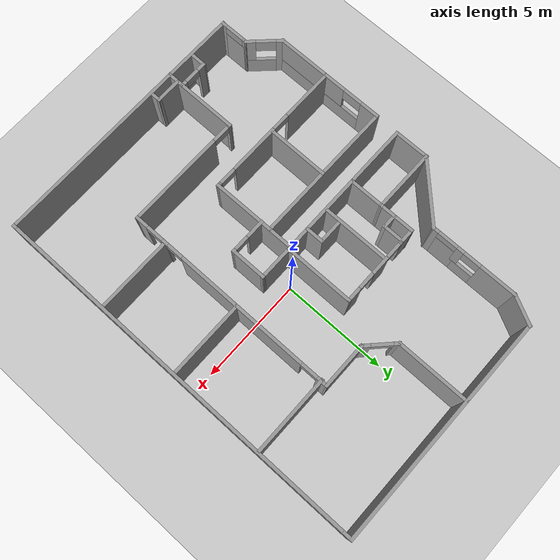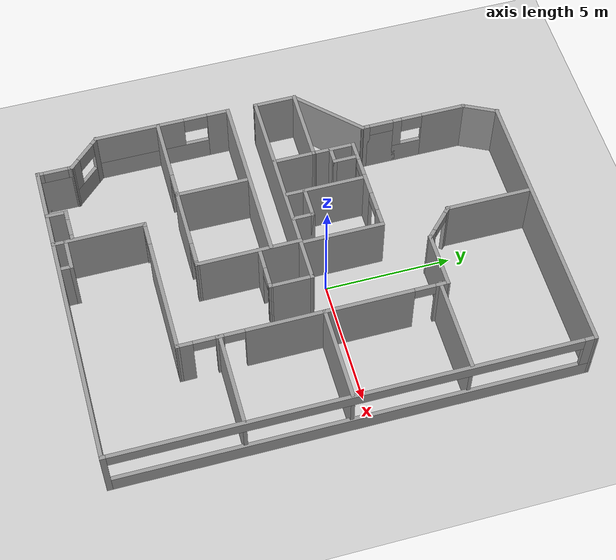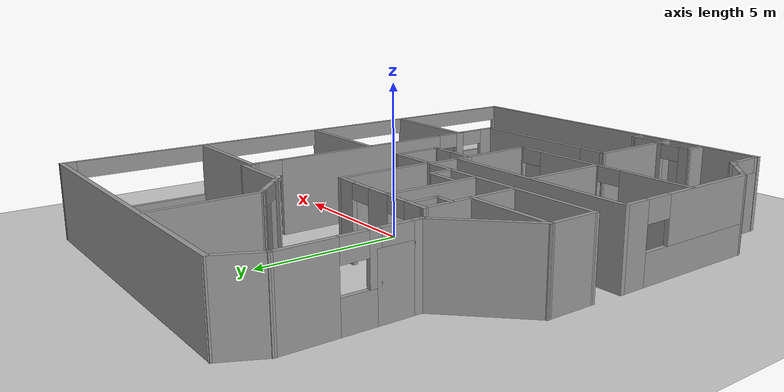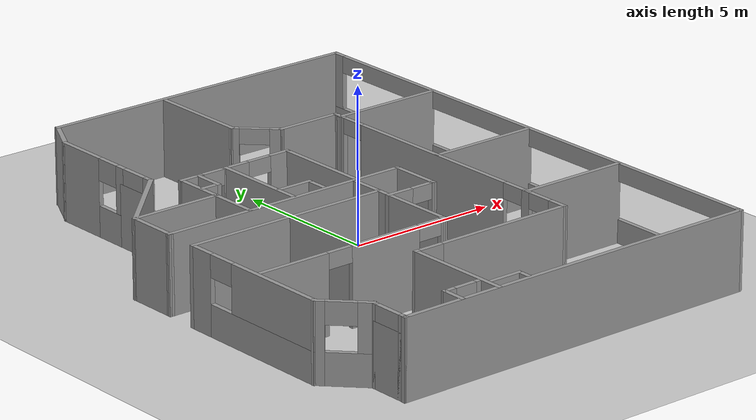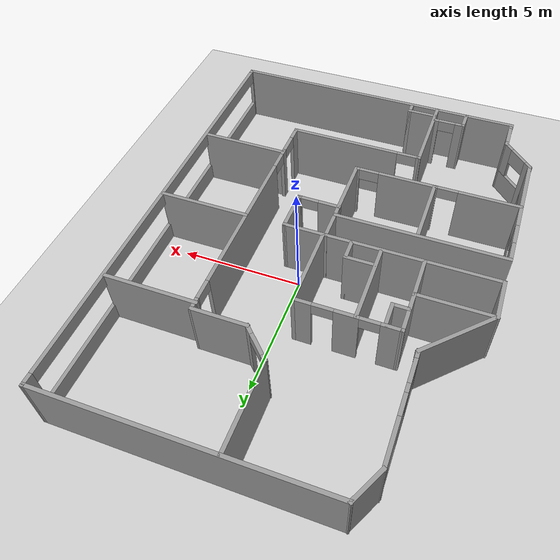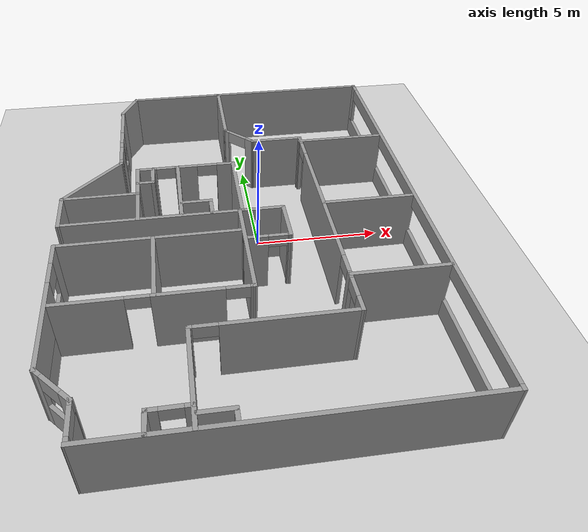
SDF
<sdf version="1.7">
 <world name="default">
  <light name="sun" type="directional">
   <pose>0 0 10 0 -0 0</pose>
   <diffuse>0.8 0.8 0.8 1</diffuse>
   <specular>0.2 0.2 0.2 1</specular>
   <attenuation>
    <range>1000</range>
    <constant>0.9</constant>
    <linear>0.01</linear>
    <quadratic>0.001</quadratic>
   </attenuation>
   <direction>-0.5 0.1 -0.9</direction>
   <spot><inner_angle>0</inner_angle><outer_angle>0</outer_angle><falloff>0</falloff></spot>
  </light>
  <model name="ground_plane">
   <static>1</static>
   <link name="link">
    <collision name="collision">
     <geometry><plane><normal>0 0 1</normal><size>100 100</size></plane></geometry>
     <surface><friction><ode><mu>100</mu><mu2>50</mu2></ode></friction></surface>
    </collision>
    <visual name="visual">
     <cast_shadows>0</cast_shadows>
     <geometry><plane><normal>0 0 1</normal><size>100 100</size></plane></geometry>
     <material>
      <script><uri>file://media/materials/scripts/gazebo.material</uri><name>Gazebo/Grey</name></script>
     </material>
    </visual>
   </link>
  </model>
  <gravity>0 0 -9.8</gravity>
  <magnetic_field>6e-06 2.3e-05 -4.2e-05</magnetic_field>
  <atmosphere type="adiabatic"/>
  <physics type="ode">
   <max_step_size>0.001</max_step_size>
   <real_time_factor>1</real_time_factor>
   <real_time_update_rate>1000</real_time_update_rate>
  </physics>
  <scene><ambient>0.4 0.4 0.4 1</ambient><background>0.7 0.7 0.7 1</background><shadows>1</shadows></scene>
  <audio><device>default</device></audio>
  <spherical_coordinates>
   <surface_model>EARTH_WGS84</surface_model>
   <latitude_deg>0</latitude_deg>
   <longitude_deg>0</longitude_deg>
   <elevation>0</elevation>
   <heading_deg>0</heading_deg>
  </spherical_coordinates>
  <model name="lake_harbour_office">
   <link name="Wall_0">
    <pose>0.435117 -5.60543 0 0 -0 2e-06</pose>
    <visual name="Wall_0_Visual_1">
     <pose>0.513518 0 1.25 0 -0 0</pose>
     <geometry><box><size>4.68067 0.15 2.5</size></box></geometry>
     <material>
      <script><uri>file://media/materials/scripts/gazebo.material</uri><name>Gazebo/Grey</name></script>
      <ambient>1 1 1 1</ambient>
      <shader type="pixel"/>
     </material>
     <meta><layer>0</layer></meta>
    </visual>
    <visual name="Wall_0_Visual_0">
     <pose>-2.75685 0 1.25 0 -0 0</pose>
     <geometry><box><size>0.194017 0.15 2.5</size></box></geometry>
     <material>
      <script><uri>file://media/materials/scripts/gazebo.material</uri><name>Gazebo/Grey</name></script>
      <ambient>1 1 1 1</ambient>
      <shader type="pixel"/>
     </material>
     <meta><layer>0</layer></meta>
    </visual>
    <visual name="Wall_0_Visual_2">
     <pose>-2.24333 0 2.25 0 -0 0</pose>
     <geometry><box><size>0.833019 0.15 0.5</size></box></geometry>
     <material>
      <script><uri>file://media/materials/scripts/gazebo.material</uri><name>Gazebo/Grey</name></script>
      <ambient>1 1 1 1</ambient>
      <shader type="pixel"/>
     </material>
     <meta><layer>0</layer></meta>
    </visual>
    <collision name="Wall_0_Collision_1">
     <pose>0.513518 0 1.25 0 -0 0</pose>
     <geometry><box><size>4.68067 0.15 2.5</size></box></geometry>
     <surface>
      <friction>
       <ode><mu>1</mu><mu2>1</mu2><fdir1>0 0 0</fdir1><slip1>0</slip1><slip2>0</slip2></ode>
       <torsional>
        <coefficient>1</coefficient>
        <patch_radius>0</patch_radius>
        <surface_radius>0</surface_radius>
        <use_patch_radius>1</use_patch_radius>
        <ode><slip>0</slip></ode>
       </torsional>
      </friction>
      <bounce><restitution_coefficient>0</restitution_coefficient><threshold>1e+06</threshold></bounce>
      <contact>
       <collide_without_contact>0</collide_without_contact>
       <collide_without_contact_bitmask>1</collide_without_contact_bitmask>
       <collide_bitmask>1</collide_bitmask>
       <ode>
        <soft_cfm>0</soft_cfm>
        <soft_erp>0.2</soft_erp>
        <kp>1e+13</kp>
        <kd>1</kd>
        <max_vel>0.01</max_vel>
        <min_depth>0</min_depth>
       </ode>
       <bullet>
        <split_impulse>1</split_impulse>
        <split_impulse_penetration_threshold>-0.01</split_impulse_penetration_threshold>
        <soft_cfm>0</soft_cfm>
        <soft_erp>0.2</soft_erp>
        <kp>1e+13</kp>
        <kd>1</kd>
       </bullet>
      </contact>
     </surface>
    </collision>
    <collision name="Wall_0_Collision_2">
     <pose>-2.24333 0 2.25 0 -0 0</pose>
     <geometry><box><size>0.833019 0.15 0.5</size></box></geometry>
     <surface>
      <friction>
       <ode><mu>1</mu><mu2>1</mu2><fdir1>0 0 0</fdir1><slip1>0</slip1><slip2>0</slip2></ode>
       <torsional>
        <coefficient>1</coefficient>
        <patch_radius>0</patch_radius>
        <surface_radius>0</surface_radius>
        <use_patch_radius>1</use_patch_radius>
        <ode><slip>0</slip></ode>
       </torsional>
      </friction>
      <bounce><restitution_coefficient>0</restitution_coefficient><threshold>1e+06</threshold></bounce>
      <contact>
       <collide_without_contact>0</collide_without_contact>
       <collide_without_contact_bitmask>1</collide_without_contact_bitmask>
       <collide_bitmask>1</collide_bitmask>
       <ode>
        <soft_cfm>0</soft_cfm>
        <soft_erp>0.2</soft_erp>
        <kp>1e+13</kp>
        <kd>1</kd>
        <max_vel>0.01</max_vel>
        <min_depth>0</min_depth>
       </ode>
       <bullet>
        <split_impulse>1</split_impulse>
        <split_impulse_penetration_threshold>-0.01</split_impulse_penetration_threshold>
        <soft_cfm>0</soft_cfm>
        <soft_erp>0.2</soft_erp>
        <kp>1e+13</kp>
        <kd>1</kd>
       </bullet>
      </contact>
     </surface>
    </collision>
    <collision name="Wall_0_Collision_0">
     <pose>-2.75685 0 1.25 0 -0 0</pose>
     <geometry><box><size>0.194017 0.15 2.5</size></box></geometry>
     <surface>
      <friction>
       <ode><mu>1</mu><mu2>1</mu2><fdir1>0 0 0</fdir1><slip1>0</slip1><slip2>0</slip2></ode>
       <torsional>
        <coefficient>1</coefficient>
        <patch_radius>0</patch_radius>
        <surface_radius>0</surface_radius>
        <use_patch_radius>1</use_patch_radius>
        <ode><slip>0</slip></ode>
       </torsional>
      </friction>
      <bounce><restitution_coefficient>0</restitution_coefficient><threshold>1e+06</threshold></bounce>
      <contact>
       <collide_without_contact>0</collide_without_contact>
       <collide_without_contact_bitmask>1</collide_without_contact_bitmask>
       <collide_bitmask>1</collide_bitmask>
       <ode>
        <soft_cfm>0</soft_cfm>
        <soft_erp>0.2</soft_erp>
        <kp>1e+13</kp>
        <kd>1</kd>
        <max_vel>0.01</max_vel>
        <min_depth>0</min_depth>
       </ode>
       <bullet>
        <split_impulse>1</split_impulse>
        <split_impulse_penetration_threshold>-0.01</split_impulse_penetration_threshold>
        <soft_cfm>0</soft_cfm>
        <soft_erp>0.2</soft_erp>
        <kp>1e+13</kp>
        <kd>1</kd>
       </bullet>
      </contact>
     </surface>
    </collision>
   </link>
   <link name="Wall_1">
    <pose>3.2104 -0.472625 0 0 -0 1.57149</pose>
    <visual name="Wall_1_Visual_3">
     <pose>4.9339 0 1.25 0 -0 0</pose>
     <geometry><box><size>0.54781 0.15 2.5</size></box></geometry>
     <material>
      <script><uri>file://media/materials/scripts/gazebo.material</uri><name>Gazebo/Grey</name></script>
      <ambient>1 1 1 1</ambient>
      <shader type="pixel"/>
     </material>
     <meta><layer>0</layer></meta>
    </visual>
    <visual name="Wall_1_Visual_6">
     <pose>4.25227 0 2.25 0 -0 0</pose>
     <geometry><box><size>0.815447 0.15 0.5</size></box></geometry>
     <material>
      <script><uri>file://media/materials/scripts/gazebo.material</uri><name>Gazebo/Grey</name></script>
      <ambient>1 1 1 1</ambient>
      <shader type="pixel"/>
     </material>
     <meta><layer>0</layer></meta>
    </visual>
    <visual name="Wall_1_Visual_0">
     <pose>-4.88335 0 1.25 0 -0 0</pose>
     <geometry><box><size>0.648917 0.15 2.5</size></box></geometry>
     <material>
      <script><uri>file://media/materials/scripts/gazebo.material</uri><name>Gazebo/Grey</name></script>
      <ambient>1 1 1 1</ambient>
      <shader type="pixel"/>
     </material>
     <meta><layer>0</layer></meta>
    </visual>
    <visual name="Wall_1_Visual_4">
     <pose>-4.1362 0 2.25 0 -0 0</pose>
     <geometry><box><size>0.845376 0.15 0.5</size></box></geometry>
     <material>
      <script><uri>file://media/materials/scripts/gazebo.material</uri><name>Gazebo/Grey</name></script>
      <ambient>1 1 1 1</ambient>
      <shader type="pixel"/>
     </material>
     <meta><layer>0</layer></meta>
    </visual>
    <visual name="Wall_1_Visual_1">
     <pose>-3.55701 0 1.25 0 -0 0</pose>
     <geometry><box><size>0.313004 0.15 2.5</size></box></geometry>
     <material>
      <script><uri>file://media/materials/scripts/gazebo.material</uri><name>Gazebo/Grey</name></script>
      <ambient>1 1 1 1</ambient>
      <shader type="pixel"/>
     </material>
     <meta><layer>0</layer></meta>
    </visual>
    <visual name="Wall_1_Visual_5">
     <pose>-3.00452 0 2.25 0 -0 0</pose>
     <geometry><box><size>0.79198 0.15 0.5</size></box></geometry>
     <material>
      <script><uri>file://media/materials/scripts/gazebo.material</uri><name>Gazebo/Grey</name></script>
      <ambient>1 1 1 1</ambient>
      <shader type="pixel"/>
     </material>
     <meta><layer>0</layer></meta>
    </visual>
    <visual name="Wall_1_Visual_2">
     <pose>0.61801 0 1.25 0 -0 0</pose>
     <geometry><box><size>6.45307 0.15 2.5</size></box></geometry>
     <material>
      <script><uri>file://media/materials/scripts/gazebo.material</uri><name>Gazebo/Grey</name></script>
      <ambient>1 1 1 1</ambient>
      <shader type="pixel"/>
     </material>
     <meta><layer>0</layer></meta>
    </visual>
    <collision name="Wall_1_Collision_2">
     <pose>0.61801 0 1.25 0 -0 0</pose>
     <geometry><box><size>6.45307 0.15 2.5</size></box></geometry>
     <surface>
      <friction>
       <ode><mu>1</mu><mu2>1</mu2><fdir1>0 0 0</fdir1><slip1>0</slip1><slip2>0</slip2></ode>
       <torsional>
        <coefficient>1</coefficient>
        <patch_radius>0</patch_radius>
        <surface_radius>0</surface_radius>
        <use_patch_radius>1</use_patch_radius>
        <ode><slip>0</slip></ode>
       </torsional>
      </friction>
      <bounce><restitution_coefficient>0</restitution_coefficient><threshold>1e+06</threshold></bounce>
      <contact>
       <collide_without_contact>0</collide_without_contact>
       <collide_without_contact_bitmask>1</collide_without_contact_bitmask>
       <collide_bitmask>1</collide_bitmask>
       <ode>
        <soft_cfm>0</soft_cfm>
        <soft_erp>0.2</soft_erp>
        <kp>1e+13</kp>
        <kd>1</kd>
        <max_vel>0.01</max_vel>
        <min_depth>0</min_depth>
       </ode>
       <bullet>
        <split_impulse>1</split_impulse>
        <split_impulse_penetration_threshold>-0.01</split_impulse_penetration_threshold>
        <soft_cfm>0</soft_cfm>
        <soft_erp>0.2</soft_erp>
        <kp>1e+13</kp>
        <kd>1</kd>
       </bullet>
      </contact>
     </surface>
    </collision>
    <collision name="Wall_1_Collision_0">
     <pose>-4.88335 0 1.25 0 -0 0</pose>
     <geometry><box><size>0.648917 0.15 2.5</size></box></geometry>
     <surface>
      <friction>
       <ode><mu>1</mu><mu2>1</mu2><fdir1>0 0 0</fdir1><slip1>0</slip1><slip2>0</slip2></ode>
       <torsional>
        <coefficient>1</coefficient>
        <patch_radius>0</patch_radius>
        <surface_radius>0</surface_radius>
        <use_patch_radius>1</use_patch_radius>
        <ode><slip>0</slip></ode>
       </torsional>
      </friction>
      <bounce><restitution_coefficient>0</restitution_coefficient><threshold>1e+06</threshold></bounce>
      <contact>
       <collide_without_contact>0</collide_without_contact>
       <collide_without_contact_bitmask>1</collide_without_contact_bitmask>
       <collide_bitmask>1</collide_bitmask>
       <ode>
        <soft_cfm>0</soft_cfm>
        <soft_erp>0.2</soft_erp>
        <kp>1e+13</kp>
        <kd>1</kd>
        <max_vel>0.01</max_vel>
        <min_depth>0</min_depth>
       </ode>
       <bullet>
        <split_impulse>1</split_impulse>
        <split_impulse_penetration_threshold>-0.01</split_impulse_penetration_threshold>
        <soft_cfm>0</soft_cfm>
        <soft_erp>0.2</soft_erp>
        <kp>1e+13</kp>
        <kd>1</kd>
       </bullet>
      </contact>
     </surface>
    </collision>
    <collision name="Wall_1_Collision_3">
     <pose>4.9339 0 1.25 0 -0 0</pose>
     <geometry><box><size>0.54781 0.15 2.5</size></box></geometry>
     <surface>
      <friction>
       <ode><mu>1</mu><mu2>1</mu2><fdir1>0 0 0</fdir1><slip1>0</slip1><slip2>0</slip2></ode>
       <torsional>
        <coefficient>1</coefficient>
        <patch_radius>0</patch_radius>
        <surface_radius>0</surface_radius>
        <use_patch_radius>1</use_patch_radius>
        <ode><slip>0</slip></ode>
       </torsional>
      </friction>
      <bounce><restitution_coefficient>0</restitution_coefficient><threshold>1e+06</threshold></bounce>
      <contact>
       <collide_without_contact>0</collide_without_contact>
       <collide_without_contact_bitmask>1</collide_without_contact_bitmask>
       <collide_bitmask>1</collide_bitmask>
       <ode>
        <soft_cfm>0</soft_cfm>
        <soft_erp>0.2</soft_erp>
        <kp>1e+13</kp>
        <kd>1</kd>
        <max_vel>0.01</max_vel>
        <min_depth>0</min_depth>
       </ode>
       <bullet>
        <split_impulse>1</split_impulse>
        <split_impulse_penetration_threshold>-0.01</split_impulse_penetration_threshold>
        <soft_cfm>0</soft_cfm>
        <soft_erp>0.2</soft_erp>
        <kp>1e+13</kp>
        <kd>1</kd>
       </bullet>
      </contact>
     </surface>
    </collision>
    <collision name="Wall_1_Collision_6">
     <pose>4.25227 0 2.25 0 -0 0</pose>
     <geometry><box><size>0.815447 0.15 0.5</size></box></geometry>
     <surface>
      <friction>
       <ode><mu>1</mu><mu2>1</mu2><fdir1>0 0 0</fdir1><slip1>0</slip1><slip2>0</slip2></ode>
       <torsional>
        <coefficient>1</coefficient>
        <patch_radius>0</patch_radius>
        <surface_radius>0</surface_radius>
        <use_patch_radius>1</use_patch_radius>
        <ode><slip>0</slip></ode>
       </torsional>
      </friction>
      <bounce><restitution_coefficient>0</restitution_coefficient><threshold>1e+06</threshold></bounce>
      <contact>
       <collide_without_contact>0</collide_without_contact>
       <collide_without_contact_bitmask>1</collide_without_contact_bitmask>
       <collide_bitmask>1</collide_bitmask>
       <ode>
        <soft_cfm>0</soft_cfm>
        <soft_erp>0.2</soft_erp>
        <kp>1e+13</kp>
        <kd>1</kd>
        <max_vel>0.01</max_vel>
        <min_depth>0</min_depth>
       </ode>
       <bullet>
        <split_impulse>1</split_impulse>
        <split_impulse_penetration_threshold>-0.01</split_impulse_penetration_threshold>
        <soft_cfm>0</soft_cfm>
        <soft_erp>0.2</soft_erp>
        <kp>1e+13</kp>
        <kd>1</kd>
       </bullet>
      </contact>
     </surface>
    </collision>
    <collision name="Wall_1_Collision_1">
     <pose>-3.55701 0 1.25 0 -0 0</pose>
     <geometry><box><size>0.313004 0.15 2.5</size></box></geometry>
     <surface>
      <friction>
       <ode><mu>1</mu><mu2>1</mu2><fdir1>0 0 0</fdir1><slip1>0</slip1><slip2>0</slip2></ode>
       <torsional>
        <coefficient>1</coefficient>
        <patch_radius>0</patch_radius>
        <surface_radius>0</surface_radius>
        <use_patch_radius>1</use_patch_radius>
        <ode><slip>0</slip></ode>
       </torsional>
      </friction>
      <bounce><restitution_coefficient>0</restitution_coefficient><threshold>1e+06</threshold></bounce>
      <contact>
       <collide_without_contact>0</collide_without_contact>
       <collide_without_contact_bitmask>1</collide_without_contact_bitmask>
       <collide_bitmask>1</collide_bitmask>
       <ode>
        <soft_cfm>0</soft_cfm>
        <soft_erp>0.2</soft_erp>
        <kp>1e+13</kp>
        <kd>1</kd>
        <max_vel>0.01</max_vel>
        <min_depth>0</min_depth>
       </ode>
       <bullet>
        <split_impulse>1</split_impulse>
        <split_impulse_penetration_threshold>-0.01</split_impulse_penetration_threshold>
        <soft_cfm>0</soft_cfm>
        <soft_erp>0.2</soft_erp>
        <kp>1e+13</kp>
        <kd>1</kd>
       </bullet>
      </contact>
     </surface>
    </collision>
    <collision name="Wall_1_Collision_4">
     <pose>-4.1362 0 2.25 0 -0 0</pose>
     <geometry><box><size>0.845376 0.15 0.5</size></box></geometry>
     <surface>
      <friction>
       <ode><mu>1</mu><mu2>1</mu2><fdir1>0 0 0</fdir1><slip1>0</slip1><slip2>0</slip2></ode>
       <torsional>
        <coefficient>1</coefficient>
        <patch_radius>0</patch_radius>
        <surface_radius>0</surface_radius>
        <use_patch_radius>1</use_patch_radius>
        <ode><slip>0</slip></ode>
       </torsional>
      </friction>
      <bounce><restitution_coefficient>0</restitution_coefficient><threshold>1e+06</threshold></bounce>
      <contact>
       <collide_without_contact>0</collide_without_contact>
       <collide_without_contact_bitmask>1</collide_without_contact_bitmask>
       <collide_bitmask>1</collide_bitmask>
       <ode>
        <soft_cfm>0</soft_cfm>
        <soft_erp>0.2</soft_erp>
        <kp>1e+13</kp>
        <kd>1</kd>
        <max_vel>0.01</max_vel>
        <min_depth>0</min_depth>
       </ode>
       <bullet>
        <split_impulse>1</split_impulse>
        <split_impulse_penetration_threshold>-0.01</split_impulse_penetration_threshold>
        <soft_cfm>0</soft_cfm>
        <soft_erp>0.2</soft_erp>
        <kp>1e+13</kp>
        <kd>1</kd>
       </bullet>
      </contact>
     </surface>
    </collision>
    <collision name="Wall_1_Collision_5">
     <pose>-3.00452 0 2.25 0 -0 0</pose>
     <geometry><box><size>0.79198 0.15 0.5</size></box></geometry>
     <surface>
      <friction>
       <ode><mu>1</mu><mu2>1</mu2><fdir1>0 0 0</fdir1><slip1>0</slip1><slip2>0</slip2></ode>
       <torsional>
        <coefficient>1</coefficient>
        <patch_radius>0</patch_radius>
        <surface_radius>0</surface_radius>
        <use_patch_radius>1</use_patch_radius>
        <ode><slip>0</slip></ode>
       </torsional>
      </friction>
      <bounce><restitution_coefficient>0</restitution_coefficient><threshold>1e+06</threshold></bounce>
      <contact>
       <collide_without_contact>0</collide_without_contact>
       <collide_without_contact_bitmask>1</collide_without_contact_bitmask>
       <collide_bitmask>1</collide_bitmask>
       <ode>
        <soft_cfm>0</soft_cfm>
        <soft_erp>0.2</soft_erp>
        <kp>1e+13</kp>
        <kd>1</kd>
        <max_vel>0.01</max_vel>
        <min_depth>0</min_depth>
       </ode>
       <bullet>
        <split_impulse>1</split_impulse>
        <split_impulse_penetration_threshold>-0.01</split_impulse_penetration_threshold>
        <soft_cfm>0</soft_cfm>
        <soft_erp>0.2</soft_erp>
        <kp>1e+13</kp>
        <kd>1</kd>
       </bullet>
      </contact>
     </surface>
    </collision>
   </link>
   <link name="Wall_13">
    <pose>1.45427 9.08491 0 0 -0 3.14142</pose>
    <visual name="Wall_13_Visual">
     <pose>0 0 1.25 0 -0 0</pose>
     <geometry><box><size>10.9751 0.15 2.5</size></box></geometry>
     <material>
      <script><uri>file://media/materials/scripts/gazebo.material</uri><name>Gazebo/Grey</name></script>
      <ambient>1 1 1 1</ambient>
      <shader type="pixel"/>
     </material>
     <meta><layer>0</layer></meta>
    </visual>
    <collision name="Wall_13_Collision">
     <pose>0 0 1.25 0 -0 0</pose>
     <geometry><box><size>10.9751 0.15 2.5</size></box></geometry>
     <surface>
      <friction>
       <ode><mu>1</mu><mu2>1</mu2><fdir1>0 0 0</fdir1><slip1>0</slip1><slip2>0</slip2></ode>
       <torsional>
        <coefficient>1</coefficient>
        <patch_radius>0</patch_radius>
        <surface_radius>0</surface_radius>
        <use_patch_radius>1</use_patch_radius>
        <ode><slip>0</slip></ode>
       </torsional>
      </friction>
      <bounce><restitution_coefficient>0</restitution_coefficient><threshold>1e+06</threshold></bounce>
      <contact>
       <collide_without_contact>0</collide_without_contact>
       <collide_without_contact_bitmask>1</collide_without_contact_bitmask>
       <collide_bitmask>1</collide_bitmask>
       <ode>
        <soft_cfm>0</soft_cfm>
        <soft_erp>0.2</soft_erp>
        <kp>1e+13</kp>
        <kd>1</kd>
        <max_vel>0.01</max_vel>
        <min_depth>0</min_depth>
       </ode>
       <bullet>
        <split_impulse>1</split_impulse>
        <split_impulse_penetration_threshold>-0.01</split_impulse_penetration_threshold>
        <soft_cfm>0</soft_cfm>
        <soft_erp>0.2</soft_erp>
        <kp>1e+13</kp>
        <kd>1</kd>
       </bullet>
      </contact>
     </surface>
    </collision>
   </link>
   <link name="Wall_17">
    <pose>6.85256 -0.013794 0 0 -0 1.56923</pose>
    <visual name="Wall_17_Visual_1">
     <pose>0.111402 0 0.375 0 -0 0</pose>
     <geometry><box><size>18.1228 0.15 0.75</size></box></geometry>
     <material>
      <script><uri>file://media/materials/scripts/gazebo.material</uri><name>Gazebo/Grey</name></script>
      <ambient>1 1 1 1</ambient>
      <shader type="pixel"/>
     </material>
     <meta><layer>0</layer></meta>
    </visual>
    <visual name="Wall_17_Visual_3">
     <pose>-0.139985 0 2.225 0 -0 0</pose>
     <geometry><box><size>17.62 0.15 0.55</size></box></geometry>
     <material>
      <script><uri>file://media/materials/scripts/gazebo.material</uri><name>Gazebo/Grey</name></script>
      <ambient>1 1 1 1</ambient>
      <shader type="pixel"/>
     </material>
     <meta><layer>0</layer></meta>
    </visual>
    <visual name="Wall_17_Visual_2">
     <pose>8.9214 0 1.625 0 -0 0</pose>
     <geometry><box><size>0.502774 0.15 1.75</size></box></geometry>
     <material>
      <script><uri>file://media/materials/scripts/gazebo.material</uri><name>Gazebo/Grey</name></script>
      <ambient>1 1 1 1</ambient>
      <shader type="pixel"/>
     </material>
     <meta><layer>0</layer></meta>
    </visual>
    <visual name="Wall_17_Visual_0">
     <pose>-9.06139 0 1.25 0 -0 0</pose>
     <geometry><box><size>0.222803 0.15 2.5</size></box></geometry>
     <material>
      <script><uri>file://media/materials/scripts/gazebo.material</uri><name>Gazebo/Grey</name></script>
      <ambient>1 1 1 1</ambient>
      <shader type="pixel"/>
     </material>
     <meta><layer>0</layer></meta>
    </visual>
    <collision name="Wall_17_Collision_1">
     <pose>0.111402 0 0.375 0 -0 0</pose>
     <geometry><box><size>18.1228 0.15 0.75</size></box></geometry>
     <surface>
      <friction>
       <ode><mu>1</mu><mu2>1</mu2><fdir1>0 0 0</fdir1><slip1>0</slip1><slip2>0</slip2></ode>
       <torsional>
        <coefficient>1</coefficient>
        <patch_radius>0</patch_radius>
        <surface_radius>0</surface_radius>
        <use_patch_radius>1</use_patch_radius>
        <ode><slip>0</slip></ode>
       </torsional>
      </friction>
      <bounce><restitution_coefficient>0</restitution_coefficient><threshold>1e+06</threshold></bounce>
      <contact>
       <collide_without_contact>0</collide_without_contact>
       <collide_without_contact_bitmask>1</collide_without_contact_bitmask>
       <collide_bitmask>1</collide_bitmask>
       <ode>
        <soft_cfm>0</soft_cfm>
        <soft_erp>0.2</soft_erp>
        <kp>1e+13</kp>
        <kd>1</kd>
        <max_vel>0.01</max_vel>
        <min_depth>0</min_depth>
       </ode>
       <bullet>
        <split_impulse>1</split_impulse>
        <split_impulse_penetration_threshold>-0.01</split_impulse_penetration_threshold>
        <soft_cfm>0</soft_cfm>
        <soft_erp>0.2</soft_erp>
        <kp>1e+13</kp>
        <kd>1</kd>
       </bullet>
      </contact>
     </surface>
    </collision>
    <collision name="Wall_17_Collision_3">
     <pose>-0.139985 0 2.225 0 -0 0</pose>
     <geometry><box><size>17.62 0.15 0.55</size></box></geometry>
     <surface>
      <friction>
       <ode><mu>1</mu><mu2>1</mu2><fdir1>0 0 0</fdir1><slip1>0</slip1><slip2>0</slip2></ode>
       <torsional>
        <coefficient>1</coefficient>
        <patch_radius>0</patch_radius>
        <surface_radius>0</surface_radius>
        <use_patch_radius>1</use_patch_radius>
        <ode><slip>0</slip></ode>
       </torsional>
      </friction>
      <bounce><restitution_coefficient>0</restitution_coefficient><threshold>1e+06</threshold></bounce>
      <contact>
       <collide_without_contact>0</collide_without_contact>
       <collide_without_contact_bitmask>1</collide_without_contact_bitmask>
       <collide_bitmask>1</collide_bitmask>
       <ode>
        <soft_cfm>0</soft_cfm>
        <soft_erp>0.2</soft_erp>
        <kp>1e+13</kp>
        <kd>1</kd>
        <max_vel>0.01</max_vel>
        <min_depth>0</min_depth>
       </ode>
       <bullet>
        <split_impulse>1</split_impulse>
        <split_impulse_penetration_threshold>-0.01</split_impulse_penetration_threshold>
        <soft_cfm>0</soft_cfm>
        <soft_erp>0.2</soft_erp>
        <kp>1e+13</kp>
        <kd>1</kd>
       </bullet>
      </contact>
     </surface>
    </collision>
    <collision name="Wall_17_Collision_2">
     <pose>8.9214 0 1.625 0 -0 0</pose>
     <geometry><box><size>0.502774 0.15 1.75</size></box></geometry>
     <surface>
      <friction>
       <ode><mu>1</mu><mu2>1</mu2><fdir1>0 0 0</fdir1><slip1>0</slip1><slip2>0</slip2></ode>
       <torsional>
        <coefficient>1</coefficient>
        <patch_radius>0</patch_radius>
        <surface_radius>0</surface_radius>
        <use_patch_radius>1</use_patch_radius>
        <ode><slip>0</slip></ode>
       </torsional>
      </friction>
      <bounce><restitution_coefficient>0</restitution_coefficient><threshold>1e+06</threshold></bounce>
      <contact>
       <collide_without_contact>0</collide_without_contact>
       <collide_without_contact_bitmask>1</collide_without_contact_bitmask>
       <collide_bitmask>1</collide_bitmask>
       <ode>
        <soft_cfm>0</soft_cfm>
        <soft_erp>0.2</soft_erp>
        <kp>1e+13</kp>
        <kd>1</kd>
        <max_vel>0.01</max_vel>
        <min_depth>0</min_depth>
       </ode>
       <bullet>
        <split_impulse>1</split_impulse>
        <split_impulse_penetration_threshold>-0.01</split_impulse_penetration_threshold>
        <soft_cfm>0</soft_cfm>
        <soft_erp>0.2</soft_erp>
        <kp>1e+13</kp>
        <kd>1</kd>
       </bullet>
      </contact>
     </surface>
    </collision>
    <collision name="Wall_17_Collision_0">
     <pose>-9.06139 0 1.25 0 -0 0</pose>
     <geometry><box><size>0.222803 0.15 2.5</size></box></geometry>
     <surface>
      <friction>
       <ode><mu>1</mu><mu2>1</mu2><fdir1>0 0 0</fdir1><slip1>0</slip1><slip2>0</slip2></ode>
       <torsional>
        <coefficient>1</coefficient>
        <patch_radius>0</patch_radius>
        <surface_radius>0</surface_radius>
        <use_patch_radius>1</use_patch_radius>
        <ode><slip>0</slip></ode>
       </torsional>
      </friction>
      <bounce><restitution_coefficient>0</restitution_coefficient><threshold>1e+06</threshold></bounce>
      <contact>
       <collide_without_contact>0</collide_without_contact>
       <collide_without_contact_bitmask>1</collide_without_contact_bitmask>
       <collide_bitmask>1</collide_bitmask>
       <ode>
        <soft_cfm>0</soft_cfm>
        <soft_erp>0.2</soft_erp>
        <kp>1e+13</kp>
        <kd>1</kd>
        <max_vel>0.01</max_vel>
        <min_depth>0</min_depth>
       </ode>
       <bullet>
        <split_impulse>1</split_impulse>
        <split_impulse_penetration_threshold>-0.01</split_impulse_penetration_threshold>
        <soft_cfm>0</soft_cfm>
        <soft_erp>0.2</soft_erp>
        <kp>1e+13</kp>
        <kd>1</kd>
       </bullet>
      </contact>
     </surface>
    </collision>
   </link>
   <link name="Wall_19">
    <pose>5.00431 -4.0195 0 0 -0 0</pose>
    <visual name="Wall_19_Visual">
     <pose>0 0 1.25 0 -0 0</pose>
     <geometry><box><size>3.67 0.15 2.5</size></box></geometry>
     <material>
      <script><uri>file://media/materials/scripts/gazebo.material</uri><name>Gazebo/Grey</name></script>
      <ambient>1 1 1 1</ambient>
      <shader type="pixel"/>
     </material>
     <meta><layer>0</layer></meta>
    </visual>
    <collision name="Wall_19_Collision">
     <pose>0 0 1.25 0 -0 0</pose>
     <geometry><box><size>3.67 0.15 2.5</size></box></geometry>
     <surface>
      <friction>
       <ode><mu>1</mu><mu2>1</mu2><fdir1>0 0 0</fdir1><slip1>0</slip1><slip2>0</slip2></ode>
       <torsional>
        <coefficient>1</coefficient>
        <patch_radius>0</patch_radius>
        <surface_radius>0</surface_radius>
        <use_patch_radius>1</use_patch_radius>
        <ode><slip>0</slip></ode>
       </torsional>
      </friction>
      <bounce><restitution_coefficient>0</restitution_coefficient><threshold>1e+06</threshold></bounce>
      <contact>
       <collide_without_contact>0</collide_without_contact>
       <collide_without_contact_bitmask>1</collide_without_contact_bitmask>
       <collide_bitmask>1</collide_bitmask>
       <ode>
        <soft_cfm>0</soft_cfm>
        <soft_erp>0.2</soft_erp>
        <kp>1e+13</kp>
        <kd>1</kd>
        <max_vel>0.01</max_vel>
        <min_depth>0</min_depth>
       </ode>
       <bullet>
        <split_impulse>1</split_impulse>
        <split_impulse_penetration_threshold>-0.01</split_impulse_penetration_threshold>
        <soft_cfm>0</soft_cfm>
        <soft_erp>0.2</soft_erp>
        <kp>1e+13</kp>
        <kd>1</kd>
       </bullet>
      </contact>
     </surface>
    </collision>
   </link>
   <link name="Wall_24">
    <pose>-2.34637 -7.35192 0 0 0 -1.57231</pose>
    <visual name="Wall_24_Visual">
     <pose>0 0 1.25 0 -0 0</pose>
     <geometry><box><size>3.64297 0.15 2.5</size></box></geometry>
     <material>
      <script><uri>file://media/materials/scripts/gazebo.material</uri><name>Gazebo/Grey</name></script>
      <ambient>1 1 1 1</ambient>
      <shader type="pixel"/>
     </material>
     <meta><layer>0</layer></meta>
    </visual>
    <collision name="Wall_24_Collision">
     <pose>0 0 1.25 0 -0 0</pose>
     <geometry><box><size>3.64297 0.15 2.5</size></box></geometry>
     <surface>
      <friction>
       <ode><mu>1</mu><mu2>1</mu2><fdir1>0 0 0</fdir1><slip1>0</slip1><slip2>0</slip2></ode>
       <torsional>
        <coefficient>1</coefficient>
        <patch_radius>0</patch_radius>
        <surface_radius>0</surface_radius>
        <use_patch_radius>1</use_patch_radius>
        <ode><slip>0</slip></ode>
       </torsional>
      </friction>
      <bounce><restitution_coefficient>0</restitution_coefficient><threshold>1e+06</threshold></bounce>
      <contact>
       <collide_without_contact>0</collide_without_contact>
       <collide_without_contact_bitmask>1</collide_without_contact_bitmask>
       <collide_bitmask>1</collide_bitmask>
       <ode>
        <soft_cfm>0</soft_cfm>
        <soft_erp>0.2</soft_erp>
        <kp>1e+13</kp>
        <kd>1</kd>
        <max_vel>0.01</max_vel>
        <min_depth>0</min_depth>
       </ode>
       <bullet>
        <split_impulse>1</split_impulse>
        <split_impulse_penetration_threshold>-0.01</split_impulse_penetration_threshold>
        <soft_cfm>0</soft_cfm>
        <soft_erp>0.2</soft_erp>
        <kp>1e+13</kp>
        <kd>1</kd>
       </bullet>
      </contact>
     </surface>
    </collision>
   </link>
   <link name="Wall_26">
    <pose>-4.26687 8.47883 0 0 0 -2.04113</pose>
    <visual name="Wall_26_Visual">
     <pose>0 0 1.25 0 -0 0</pose>
     <geometry><box><size>1.5119 0.15 2.5</size></box></geometry>
     <material>
      <script><uri>file://media/materials/scripts/gazebo.material</uri><name>Gazebo/Grey</name></script>
      <ambient>1 1 1 1</ambient>
      <shader type="pixel"/>
     </material>
     <meta><layer>0</layer></meta>
    </visual>
    <collision name="Wall_26_Collision">
     <pose>0 0 1.25 0 -0 0</pose>
     <geometry><box><size>1.5119 0.15 2.5</size></box></geometry>
     <surface>
      <friction>
       <ode><mu>1</mu><mu2>1</mu2><fdir1>0 0 0</fdir1><slip1>0</slip1><slip2>0</slip2></ode>
       <torsional>
        <coefficient>1</coefficient>
        <patch_radius>0</patch_radius>
        <surface_radius>0</surface_radius>
        <use_patch_radius>1</use_patch_radius>
        <ode><slip>0</slip></ode>
       </torsional>
      </friction>
      <bounce><restitution_coefficient>0</restitution_coefficient><threshold>1e+06</threshold></bounce>
      <contact>
       <collide_without_contact>0</collide_without_contact>
       <collide_without_contact_bitmask>1</collide_without_contact_bitmask>
       <collide_bitmask>1</collide_bitmask>
       <ode>
        <soft_cfm>0</soft_cfm>
        <soft_erp>0.2</soft_erp>
        <kp>1e+13</kp>
        <kd>1</kd>
        <max_vel>0.01</max_vel>
        <min_depth>0</min_depth>
       </ode>
       <bullet>
        <split_impulse>1</split_impulse>
        <split_impulse_penetration_threshold>-0.01</split_impulse_penetration_threshold>
        <soft_cfm>0</soft_cfm>
        <soft_erp>0.2</soft_erp>
        <kp>1e+13</kp>
        <kd>1</kd>
       </bullet>
      </contact>
     </surface>
    </collision>
   </link>
   <link name="Wall_28">
    <pose>-4.57547 5.77869 0 0 0 -1.5708</pose>
    <inertial>
     <mass>1</mass>
     <inertia><ixx>1</ixx><ixy>0</ixy><ixz>0</ixz><iyy>1</iyy><iyz>0</iyz><izz>1</izz></inertia>
    </inertial>
    <visual name="Wall_28_Visual_5">
     <pose>1.32226 0 2.25 0 -0 0</pose>
     <geometry><box><size>0.960993 0.15 0.5</size></box></geometry>
     <material>
      <script><uri>file://media/materials/scripts/gazebo.material</uri><name>Gazebo/Grey</name></script>
      <ambient>1 1 1 1</ambient>
      <shader type="pixel"><normal_map>__default__</normal_map></shader>
      <diffuse>0.7 0.7 0.7 1</diffuse>
      <specular>0.01 0.01 0.01 1</specular>
      <emissive>0 0 0 1</emissive>
     </material>
     <meta><layer>0</layer></meta>
    </visual>
    <visual name="Wall_28_Visual_4">
     <pose>0.066565 0 2.15 0 -0 0</pose>
     <geometry><box><size>0.840547 0.15 0.7</size></box></geometry>
     <material>
      <script><uri>file://media/materials/scripts/gazebo.material</uri><name>Gazebo/Grey</name></script>
      <ambient>1 1 1 1</ambient>
      <shader type="pixel"><normal_map>__default__</normal_map></shader>
      <diffuse>0.7 0.7 0.7 1</diffuse>
      <specular>0.01 0.01 0.01 1</specular>
      <emissive>0 0 0 1</emissive>
     </material>
     <meta><layer>0</layer></meta>
    </visual>
    <visual name="Wall_28_Visual_0">
     <pose>-1.26092 0 1.25 0 -0 0</pose>
     <geometry><box><size>1.81443 0.15 2.5</size></box></geometry>
     <material>
      <script><uri>file://media/materials/scripts/gazebo.material</uri><name>Gazebo/Grey</name></script>
      <ambient>1 1 1 1</ambient>
      <shader type="pixel"><normal_map>__default__</normal_map></shader>
      <diffuse>0.7 0.7 0.7 1</diffuse>
      <specular>0.01 0.01 0.01 1</specular>
      <emissive>0 0 0 1</emissive>
     </material>
     <meta><layer>0</layer></meta>
    </visual>
    <visual name="Wall_28_Visual_2">
     <pose>0.244026 0 0.5 0 -0 0</pose>
     <geometry><box><size>1.19547 0.15 1</size></box></geometry>
     <material>
      <script><uri>file://media/materials/scripts/gazebo.material</uri><name>Gazebo/Grey</name></script>
      <ambient>1 1 1 1</ambient>
      <shader type="pixel"><normal_map>__default__</normal_map></shader>
      <diffuse>0.7 0.7 0.7 1</diffuse>
      <specular>0.01 0.01 0.01 1</specular>
      <emissive>0 0 0 1</emissive>
     </material>
     <meta><layer>0</layer></meta>
    </visual>
    <visual name="Wall_28_Visual_3">
     <pose>0.6643 0 1.75 0 -0 0</pose>
     <geometry><box><size>0.354924 0.15 1.5</size></box></geometry>
     <material>
      <script><uri>file://media/materials/scripts/gazebo.material</uri><name>Gazebo/Grey</name></script>
      <ambient>1 1 1 1</ambient>
      <shader type="pixel"><normal_map>__default__</normal_map></shader>
      <diffuse>0.7 0.7 0.7 1</diffuse>
      <specular>0.01 0.01 0.01 1</specular>
      <emissive>0 0 0 1</emissive>
     </material>
     <meta><layer>0</layer></meta>
    </visual>
    <visual name="Wall_28_Visual_1">
     <pose>1.98545 0 1.25 0 -0 0</pose>
     <geometry><box><size>0.365381 0.15 2.5</size></box></geometry>
     <material>
      <script><uri>file://media/materials/scripts/gazebo.material</uri><name>Gazebo/Grey</name></script>
      <ambient>1 1 1 1</ambient>
      <shader type="pixel"><normal_map>__default__</normal_map></shader>
      <diffuse>0.7 0.7 0.7 1</diffuse>
      <specular>0.01 0.01 0.01 1</specular>
      <emissive>0 0 0 1</emissive>
     </material>
     <meta><layer>0</layer></meta>
    </visual>
    <visual name="ModelPreview_5::Wall_28::visual_6">
     <pose>1.3 0 1 0 -0 0</pose>
     <geometry><box><size>1.2 0.15 2</size></box></geometry>
     <material>
      <script><uri>file://media/materials/scripts/gazebo.material</uri><name>Gazebo/Grey</name></script>
      <ambient>1 1 1 1</ambient>
      <shader type="pixel"><normal_map>__default__</normal_map></shader>
      <diffuse>0.7 0.7 0.7 1</diffuse>
      <specular>0.01 0.01 0.01 1</specular>
      <emissive>0 0 0 1</emissive>
     </material>
     <meta><layer>0</layer></meta>
    </visual>
    <collision name="Wall_28_Collision_5">
     <pose>1.32226 0 2.25 0 -0 0</pose>
     <geometry><box><size>0.960993 0.15 0.5</size></box></geometry>
     <surface>
      <friction>
       <ode><mu>1</mu><mu2>1</mu2><fdir1>0 0 0</fdir1><slip1>0</slip1><slip2>0</slip2></ode>
       <torsional>
        <coefficient>1</coefficient>
        <patch_radius>0</patch_radius>
        <surface_radius>0</surface_radius>
        <use_patch_radius>1</use_patch_radius>
        <ode><slip>0</slip></ode>
       </torsional>
      </friction>
      <bounce><restitution_coefficient>0</restitution_coefficient><threshold>1e+06</threshold></bounce>
      <contact>
       <collide_without_contact>0</collide_without_contact>
       <collide_without_contact_bitmask>1</collide_without_contact_bitmask>
       <collide_bitmask>1</collide_bitmask>
       <ode>
        <soft_cfm>0</soft_cfm>
        <soft_erp>0.2</soft_erp>
        <kp>1e+13</kp>
        <kd>1</kd>
        <max_vel>0.01</max_vel>
        <min_depth>0</min_depth>
       </ode>
       <bullet>
        <split_impulse>1</split_impulse>
        <split_impulse_penetration_threshold>-0.01</split_impulse_penetration_threshold>
        <soft_cfm>0</soft_cfm>
        <soft_erp>0.2</soft_erp>
        <kp>1e+13</kp>
        <kd>1</kd>
       </bullet>
      </contact>
     </surface>
    </collision>
    <collision name="Wall_28_Collision_4">
     <pose>0.066565 0 2.15 0 -0 0</pose>
     <geometry><box><size>0.840547 0.15 0.7</size></box></geometry>
     <surface>
      <friction>
       <ode><mu>1</mu><mu2>1</mu2><fdir1>0 0 0</fdir1><slip1>0</slip1><slip2>0</slip2></ode>
       <torsional>
        <coefficient>1</coefficient>
        <patch_radius>0</patch_radius>
        <surface_radius>0</surface_radius>
        <use_patch_radius>1</use_patch_radius>
        <ode><slip>0</slip></ode>
       </torsional>
      </friction>
      <bounce><restitution_coefficient>0</restitution_coefficient><threshold>1e+06</threshold></bounce>
      <contact>
       <collide_without_contact>0</collide_without_contact>
       <collide_without_contact_bitmask>1</collide_without_contact_bitmask>
       <collide_bitmask>1</collide_bitmask>
       <ode>
        <soft_cfm>0</soft_cfm>
        <soft_erp>0.2</soft_erp>
        <kp>1e+13</kp>
        <kd>1</kd>
        <max_vel>0.01</max_vel>
        <min_depth>0</min_depth>
       </ode>
       <bullet>
        <split_impulse>1</split_impulse>
        <split_impulse_penetration_threshold>-0.01</split_impulse_penetration_threshold>
        <soft_cfm>0</soft_cfm>
        <soft_erp>0.2</soft_erp>
        <kp>1e+13</kp>
        <kd>1</kd>
       </bullet>
      </contact>
     </surface>
    </collision>
    <collision name="Wall_28_Collision_2">
     <pose>0.244026 0 0.5 0 -0 0</pose>
     <geometry><box><size>1.19547 0.15 1</size></box></geometry>
     <surface>
      <friction>
       <ode><mu>1</mu><mu2>1</mu2><fdir1>0 0 0</fdir1><slip1>0</slip1><slip2>0</slip2></ode>
       <torsional>
        <coefficient>1</coefficient>
        <patch_radius>0</patch_radius>
        <surface_radius>0</surface_radius>
        <use_patch_radius>1</use_patch_radius>
        <ode><slip>0</slip></ode>
       </torsional>
      </friction>
      <bounce><restitution_coefficient>0</restitution_coefficient><threshold>1e+06</threshold></bounce>
      <contact>
       <collide_without_contact>0</collide_without_contact>
       <collide_without_contact_bitmask>1</collide_without_contact_bitmask>
       <collide_bitmask>1</collide_bitmask>
       <ode>
        <soft_cfm>0</soft_cfm>
        <soft_erp>0.2</soft_erp>
        <kp>1e+13</kp>
        <kd>1</kd>
        <max_vel>0.01</max_vel>
        <min_depth>0</min_depth>
       </ode>
       <bullet>
        <split_impulse>1</split_impulse>
        <split_impulse_penetration_threshold>-0.01</split_impulse_penetration_threshold>
        <soft_cfm>0</soft_cfm>
        <soft_erp>0.2</soft_erp>
        <kp>1e+13</kp>
        <kd>1</kd>
       </bullet>
      </contact>
     </surface>
    </collision>
    <collision name="collision_6">
     <pose>1.3 0 1 0 -0 0</pose>
     <geometry><box><size>1.2 0.15 2</size></box></geometry>
     <surface>
      <friction>
       <ode><mu>1</mu><mu2>1</mu2><fdir1>0 0 0</fdir1><slip1>0</slip1><slip2>0</slip2></ode>
       <torsional>
        <coefficient>1</coefficient>
        <patch_radius>0</patch_radius>
        <surface_radius>0</surface_radius>
        <use_patch_radius>1</use_patch_radius>
        <ode><slip>0</slip></ode>
       </torsional>
      </friction>
      <bounce><restitution_coefficient>0</restitution_coefficient><threshold>1e+06</threshold></bounce>
      <contact>
       <collide_without_contact>0</collide_without_contact>
       <collide_without_contact_bitmask>1</collide_without_contact_bitmask>
       <collide_bitmask>1</collide_bitmask>
       <ode>
        <soft_cfm>0</soft_cfm>
        <soft_erp>0.2</soft_erp>
        <kp>1e+13</kp>
        <kd>1</kd>
        <max_vel>0.01</max_vel>
        <min_depth>0</min_depth>
       </ode>
       <bullet>
        <split_impulse>1</split_impulse>
        <split_impulse_penetration_threshold>-0.01</split_impulse_penetration_threshold>
        <soft_cfm>0</soft_cfm>
        <soft_erp>0.2</soft_erp>
        <kp>1e+13</kp>
        <kd>1</kd>
       </bullet>
      </contact>
     </surface>
    </collision>
    <collision name="Wall_28_Collision_3">
     <pose>0.6643 0 1.75 0 -0 0</pose>
     <geometry><box><size>0.354924 0.15 1.5</size></box></geometry>
     <surface>
      <friction>
       <ode><mu>1</mu><mu2>1</mu2><fdir1>0 0 0</fdir1><slip1>0</slip1><slip2>0</slip2></ode>
       <torsional>
        <coefficient>1</coefficient>
        <patch_radius>0</patch_radius>
        <surface_radius>0</surface_radius>
        <use_patch_radius>1</use_patch_radius>
        <ode><slip>0</slip></ode>
       </torsional>
      </friction>
      <bounce><restitution_coefficient>0</restitution_coefficient><threshold>1e+06</threshold></bounce>
      <contact>
       <collide_without_contact>0</collide_without_contact>
       <collide_without_contact_bitmask>1</collide_without_contact_bitmask>
       <collide_bitmask>1</collide_bitmask>
       <ode>
        <soft_cfm>0</soft_cfm>
        <soft_erp>0.2</soft_erp>
        <kp>1e+13</kp>
        <kd>1</kd>
        <max_vel>0.01</max_vel>
        <min_depth>0</min_depth>
       </ode>
       <bullet>
        <split_impulse>1</split_impulse>
        <split_impulse_penetration_threshold>-0.01</split_impulse_penetration_threshold>
        <soft_cfm>0</soft_cfm>
        <soft_erp>0.2</soft_erp>
        <kp>1e+13</kp>
        <kd>1</kd>
       </bullet>
      </contact>
     </surface>
    </collision>
    <collision name="Wall_28_Collision_1">
     <pose>1.98545 0 1.25 0 -0 0</pose>
     <geometry><box><size>0.365381 0.15 2.5</size></box></geometry>
     <surface>
      <friction>
       <ode><mu>1</mu><mu2>1</mu2><fdir1>0 0 0</fdir1><slip1>0</slip1><slip2>0</slip2></ode>
       <torsional>
        <coefficient>1</coefficient>
        <patch_radius>0</patch_radius>
        <surface_radius>0</surface_radius>
        <use_patch_radius>1</use_patch_radius>
        <ode><slip>0</slip></ode>
       </torsional>
      </friction>
      <bounce><restitution_coefficient>0</restitution_coefficient><threshold>1e+06</threshold></bounce>
      <contact>
       <collide_without_contact>0</collide_without_contact>
       <collide_without_contact_bitmask>1</collide_without_contact_bitmask>
       <collide_bitmask>1</collide_bitmask>
       <ode>
        <soft_cfm>0</soft_cfm>
        <soft_erp>0.2</soft_erp>
        <kp>1e+13</kp>
        <kd>1</kd>
        <max_vel>0.01</max_vel>
        <min_depth>0</min_depth>
       </ode>
       <bullet>
        <split_impulse>1</split_impulse>
        <split_impulse_penetration_threshold>-0.01</split_impulse_penetration_threshold>
        <soft_cfm>0</soft_cfm>
        <soft_erp>0.2</soft_erp>
        <kp>1e+13</kp>
        <kd>1</kd>
       </bullet>
      </contact>
     </surface>
    </collision>
    <collision name="Wall_28_Collision_0">
     <pose>-1.26092 0 1.25 0 -0 0</pose>
     <geometry><box><size>1.81443 0.15 2.5</size></box></geometry>
     <surface>
      <friction>
       <ode><mu>1</mu><mu2>1</mu2><fdir1>0 0 0</fdir1><slip1>0</slip1><slip2>0</slip2></ode>
       <torsional>
        <coefficient>1</coefficient>
        <patch_radius>0</patch_radius>
        <surface_radius>0</surface_radius>
        <use_patch_radius>1</use_patch_radius>
        <ode><slip>0</slip></ode>
       </torsional>
      </friction>
      <bounce><restitution_coefficient>0</restitution_coefficient><threshold>1e+06</threshold></bounce>
      <contact>
       <collide_without_contact>0</collide_without_contact>
       <collide_without_contact_bitmask>1</collide_without_contact_bitmask>
       <collide_bitmask>1</collide_bitmask>
       <ode>
        <soft_cfm>0</soft_cfm>
        <soft_erp>0.2</soft_erp>
        <kp>1e+13</kp>
        <kd>1</kd>
        <max_vel>0.01</max_vel>
        <min_depth>0</min_depth>
       </ode>
       <bullet>
        <split_impulse>1</split_impulse>
        <split_impulse_penetration_threshold>-0.01</split_impulse_penetration_threshold>
        <soft_cfm>0</soft_cfm>
        <soft_erp>0.2</soft_erp>
        <kp>1e+13</kp>
        <kd>1</kd>
       </bullet>
      </contact>
     </surface>
    </collision>
   </link>
   <link name="Wall_30">
    <pose>-5.6836 2.58621 0 0 0 -2.36018</pose>
    <visual name="Wall_30_Visual">
     <pose>0 0 1.25 0 -0 0</pose>
     <geometry><box><size>3.27185 0.15 2.5</size></box></geometry>
     <material>
      <script><uri>file://media/materials/scripts/gazebo.material</uri><name>Gazebo/Grey</name></script>
      <ambient>1 1 1 1</ambient>
      <shader type="pixel"/>
     </material>
     <meta><layer>0</layer></meta>
    </visual>
    <collision name="Wall_30_Collision">
     <pose>0 0 1.25 0 -0 0</pose>
     <geometry><box><size>3.27185 0.15 2.5</size></box></geometry>
     <surface>
      <friction>
       <ode><mu>1</mu><mu2>1</mu2><fdir1>0 0 0</fdir1><slip1>0</slip1><slip2>0</slip2></ode>
       <torsional>
        <coefficient>1</coefficient>
        <patch_radius>0</patch_radius>
        <surface_radius>0</surface_radius>
        <use_patch_radius>1</use_patch_radius>
        <ode><slip>0</slip></ode>
       </torsional>
      </friction>
      <bounce><restitution_coefficient>0</restitution_coefficient><threshold>1e+06</threshold></bounce>
      <contact>
       <collide_without_contact>0</collide_without_contact>
       <collide_without_contact_bitmask>1</collide_without_contact_bitmask>
       <collide_bitmask>1</collide_bitmask>
       <ode>
        <soft_cfm>0</soft_cfm>
        <soft_erp>0.2</soft_erp>
        <kp>1e+13</kp>
        <kd>1</kd>
        <max_vel>0.01</max_vel>
        <min_depth>0</min_depth>
       </ode>
       <bullet>
        <split_impulse>1</split_impulse>
        <split_impulse_penetration_threshold>-0.01</split_impulse_penetration_threshold>
        <soft_cfm>0</soft_cfm>
        <soft_erp>0.2</soft_erp>
        <kp>1e+13</kp>
        <kd>1</kd>
       </bullet>
      </contact>
     </surface>
    </collision>
   </link>
   <link name="Wall_32">
    <pose>-6.80053 0.686876 0 0 0 -1.5708</pose>
    <visual name="Wall_32_Visual">
     <pose>0 0 1.25 0 -0 0</pose>
     <geometry><box><size>1.75 0.15 2.5</size></box></geometry>
     <material>
      <script><uri>file://media/materials/scripts/gazebo.material</uri><name>Gazebo/Grey</name></script>
      <ambient>1 1 1 1</ambient>
      <shader type="pixel"/>
     </material>
     <meta><layer>0</layer></meta>
    </visual>
    <collision name="Wall_32_Collision">
     <pose>0 0 1.25 0 -0 0</pose>
     <geometry><box><size>1.75 0.15 2.5</size></box></geometry>
     <surface>
      <friction>
       <ode><mu>1</mu><mu2>1</mu2><fdir1>0 0 0</fdir1><slip1>0</slip1><slip2>0</slip2></ode>
       <torsional>
        <coefficient>1</coefficient>
        <patch_radius>0</patch_radius>
        <surface_radius>0</surface_radius>
        <use_patch_radius>1</use_patch_radius>
        <ode><slip>0</slip></ode>
       </torsional>
      </friction>
      <bounce><restitution_coefficient>0</restitution_coefficient><threshold>1e+06</threshold></bounce>
      <contact>
       <collide_without_contact>0</collide_without_contact>
       <collide_without_contact_bitmask>1</collide_without_contact_bitmask>
       <collide_bitmask>1</collide_bitmask>
       <ode>
        <soft_cfm>0</soft_cfm>
        <soft_erp>0.2</soft_erp>
        <kp>1e+13</kp>
        <kd>1</kd>
        <max_vel>0.01</max_vel>
        <min_depth>0</min_depth>
       </ode>
       <bullet>
        <split_impulse>1</split_impulse>
        <split_impulse_penetration_threshold>-0.01</split_impulse_penetration_threshold>
        <soft_cfm>0</soft_cfm>
        <soft_erp>0.2</soft_erp>
        <kp>1e+13</kp>
        <kd>1</kd>
       </bullet>
      </contact>
     </surface>
    </collision>
   </link>
   <link name="Wall_34">
    <pose>-2.59189 -0.111503 0 0 -0 0.000385</pose>
    <visual name="Wall_34_Visual">
     <pose>0 0 1.25 0 -0 0</pose>
     <geometry><box><size>8.56728 0.15 2.5</size></box></geometry>
     <material>
      <script><uri>file://media/materials/scripts/gazebo.material</uri><name>Gazebo/Grey</name></script>
      <ambient>1 1 1 1</ambient>
      <shader type="pixel"/>
     </material>
     <meta><layer>0</layer></meta>
    </visual>
    <collision name="Wall_34_Collision">
     <pose>0 0 1.25 0 -0 0</pose>
     <geometry><box><size>8.56728 0.15 2.5</size></box></geometry>
     <surface>
      <friction>
       <ode><mu>1</mu><mu2>1</mu2><fdir1>0 0 0</fdir1><slip1>0</slip1><slip2>0</slip2></ode>
       <torsional>
        <coefficient>1</coefficient>
        <patch_radius>0</patch_radius>
        <surface_radius>0</surface_radius>
        <use_patch_radius>1</use_patch_radius>
        <ode><slip>0</slip></ode>
       </torsional>
      </friction>
      <bounce><restitution_coefficient>0</restitution_coefficient><threshold>1e+06</threshold></bounce>
      <contact>
       <collide_without_contact>0</collide_without_contact>
       <collide_without_contact_bitmask>1</collide_without_contact_bitmask>
       <collide_bitmask>1</collide_bitmask>
       <ode>
        <soft_cfm>0</soft_cfm>
        <soft_erp>0.2</soft_erp>
        <kp>1e+13</kp>
        <kd>1</kd>
        <max_vel>0.01</max_vel>
        <min_depth>0</min_depth>
       </ode>
       <bullet>
        <split_impulse>1</split_impulse>
        <split_impulse_penetration_threshold>-0.01</split_impulse_penetration_threshold>
        <soft_cfm>0</soft_cfm>
        <soft_erp>0.2</soft_erp>
        <kp>1e+13</kp>
        <kd>1</kd>
       </bullet>
      </contact>
     </surface>
    </collision>
   </link>
   <link name="Wall_38">
    <pose>2.15684 4.66018 0 0 -0 3.14159</pose>
    <visual name="Wall_38_Visual">
     <pose>0 0 1.25 0 -0 0</pose>
     <geometry><box><size>2.25 0.15 2.5</size></box></geometry>
     <material>
      <script><uri>file://media/materials/scripts/gazebo.material</uri><name>Gazebo/Grey</name></script>
      <ambient>1 1 1 1</ambient>
      <shader type="pixel"/>
     </material>
     <meta><layer>0</layer></meta>
    </visual>
    <collision name="Wall_38_Collision">
     <pose>0 0 1.25 0 -0 0</pose>
     <geometry><box><size>2.25 0.15 2.5</size></box></geometry>
     <surface>
      <friction>
       <ode><mu>1</mu><mu2>1</mu2><fdir1>0 0 0</fdir1><slip1>0</slip1><slip2>0</slip2></ode>
       <torsional>
        <coefficient>1</coefficient>
        <patch_radius>0</patch_radius>
        <surface_radius>0</surface_radius>
        <use_patch_radius>1</use_patch_radius>
        <ode><slip>0</slip></ode>
       </torsional>
      </friction>
      <bounce><restitution_coefficient>0</restitution_coefficient><threshold>1e+06</threshold></bounce>
      <contact>
       <collide_without_contact>0</collide_without_contact>
       <collide_without_contact_bitmask>1</collide_without_contact_bitmask>
       <collide_bitmask>1</collide_bitmask>
       <ode>
        <soft_cfm>0</soft_cfm>
        <soft_erp>0.2</soft_erp>
        <kp>1e+13</kp>
        <kd>1</kd>
        <max_vel>0.01</max_vel>
        <min_depth>0</min_depth>
       </ode>
       <bullet>
        <split_impulse>1</split_impulse>
        <split_impulse_penetration_threshold>-0.01</split_impulse_penetration_threshold>
        <soft_cfm>0</soft_cfm>
        <soft_erp>0.2</soft_erp>
        <kp>1e+13</kp>
        <kd>1</kd>
       </bullet>
      </contact>
     </surface>
    </collision>
   </link>
   <link name="Wall_39">
    <pose>0.56627 5.18296 0 0 -0 2.37292</pose>
    <visual name="Wall_39_Visual_0">
     <pose>-0.606997 0 1.25 0 -0 0</pose>
     <geometry><box><size>0.440013 0.15 2.5</size></box></geometry>
     <material>
      <script><uri>file://media/materials/scripts/gazebo.material</uri><name>Gazebo/Grey</name></script>
      <ambient>1 1 1 1</ambient>
      <shader type="pixel"/>
     </material>
     <meta><layer>0</layer></meta>
    </visual>
    <visual name="Wall_39_Visual_2">
     <pose>0.069956 0 2.25 0 -0 0</pose>
     <geometry><box><size>0.913893 0.15 0.5</size></box></geometry>
     <material>
      <script><uri>file://media/materials/scripts/gazebo.material</uri><name>Gazebo/Grey</name></script>
      <ambient>1 1 1 1</ambient>
      <shader type="pixel"/>
     </material>
     <meta><layer>0</layer></meta>
    </visual>
    <visual name="Wall_39_Visual_1">
     <pose>0.676953 0 1.25 0 -0 0</pose>
     <geometry><box><size>0.300101 0.15 2.5</size></box></geometry>
     <material>
      <script><uri>file://media/materials/scripts/gazebo.material</uri><name>Gazebo/Grey</name></script>
      <ambient>1 1 1 1</ambient>
      <shader type="pixel"/>
     </material>
     <meta><layer>0</layer></meta>
    </visual>
    <collision name="Wall_39_Collision_1">
     <pose>0.676953 0 1.25 0 -0 0</pose>
     <geometry><box><size>0.300101 0.15 2.5</size></box></geometry>
     <surface>
      <friction>
       <ode><mu>1</mu><mu2>1</mu2><fdir1>0 0 0</fdir1><slip1>0</slip1><slip2>0</slip2></ode>
       <torsional>
        <coefficient>1</coefficient>
        <patch_radius>0</patch_radius>
        <surface_radius>0</surface_radius>
        <use_patch_radius>1</use_patch_radius>
        <ode><slip>0</slip></ode>
       </torsional>
      </friction>
      <bounce><restitution_coefficient>0</restitution_coefficient><threshold>1e+06</threshold></bounce>
      <contact>
       <collide_without_contact>0</collide_without_contact>
       <collide_without_contact_bitmask>1</collide_without_contact_bitmask>
       <collide_bitmask>1</collide_bitmask>
       <ode>
        <soft_cfm>0</soft_cfm>
        <soft_erp>0.2</soft_erp>
        <kp>1e+13</kp>
        <kd>1</kd>
        <max_vel>0.01</max_vel>
        <min_depth>0</min_depth>
       </ode>
       <bullet>
        <split_impulse>1</split_impulse>
        <split_impulse_penetration_threshold>-0.01</split_impulse_penetration_threshold>
        <soft_cfm>0</soft_cfm>
        <soft_erp>0.2</soft_erp>
        <kp>1e+13</kp>
        <kd>1</kd>
       </bullet>
      </contact>
     </surface>
    </collision>
    <collision name="Wall_39_Collision_0">
     <pose>-0.606997 0 1.25 0 -0 0</pose>
     <geometry><box><size>0.440013 0.15 2.5</size></box></geometry>
     <surface>
      <friction>
       <ode><mu>1</mu><mu2>1</mu2><fdir1>0 0 0</fdir1><slip1>0</slip1><slip2>0</slip2></ode>
       <torsional>
        <coefficient>1</coefficient>
        <patch_radius>0</patch_radius>
        <surface_radius>0</surface_radius>
        <use_patch_radius>1</use_patch_radius>
        <ode><slip>0</slip></ode>
       </torsional>
      </friction>
      <bounce><restitution_coefficient>0</restitution_coefficient><threshold>1e+06</threshold></bounce>
      <contact>
       <collide_without_contact>0</collide_without_contact>
       <collide_without_contact_bitmask>1</collide_without_contact_bitmask>
       <collide_bitmask>1</collide_bitmask>
       <ode>
        <soft_cfm>0</soft_cfm>
        <soft_erp>0.2</soft_erp>
        <kp>1e+13</kp>
        <kd>1</kd>
        <max_vel>0.01</max_vel>
        <min_depth>0</min_depth>
       </ode>
       <bullet>
        <split_impulse>1</split_impulse>
        <split_impulse_penetration_threshold>-0.01</split_impulse_penetration_threshold>
        <soft_cfm>0</soft_cfm>
        <soft_erp>0.2</soft_erp>
        <kp>1e+13</kp>
        <kd>1</kd>
       </bullet>
      </contact>
     </surface>
    </collision>
    <collision name="Wall_39_Collision_2">
     <pose>0.069956 0 2.25 0 -0 0</pose>
     <geometry><box><size>0.913893 0.15 0.5</size></box></geometry>
     <surface>
      <friction>
       <ode><mu>1</mu><mu2>1</mu2><fdir1>0 0 0</fdir1><slip1>0</slip1><slip2>0</slip2></ode>
       <torsional>
        <coefficient>1</coefficient>
        <patch_radius>0</patch_radius>
        <surface_radius>0</surface_radius>
        <use_patch_radius>1</use_patch_radius>
        <ode><slip>0</slip></ode>
       </torsional>
      </friction>
      <bounce><restitution_coefficient>0</restitution_coefficient><threshold>1e+06</threshold></bounce>
      <contact>
       <collide_without_contact>0</collide_without_contact>
       <collide_without_contact_bitmask>1</collide_without_contact_bitmask>
       <collide_bitmask>1</collide_bitmask>
       <ode>
        <soft_cfm>0</soft_cfm>
        <soft_erp>0.2</soft_erp>
        <kp>1e+13</kp>
        <kd>1</kd>
        <max_vel>0.01</max_vel>
        <min_depth>0</min_depth>
       </ode>
       <bullet>
        <split_impulse>1</split_impulse>
        <split_impulse_penetration_threshold>-0.01</split_impulse_penetration_threshold>
        <soft_cfm>0</soft_cfm>
        <soft_erp>0.2</soft_erp>
        <kp>1e+13</kp>
        <kd>1</kd>
       </bullet>
      </contact>
     </surface>
    </collision>
   </link>
   <link name="Wall_43">
    <pose>0.025706 7.38074 0 0 -0 1.5708</pose>
    <visual name="Wall_43_Visual">
     <pose>0 0 1.25 0 -0 0</pose>
     <geometry><box><size>3.5 0.15 2.5</size></box></geometry>
     <material>
      <script><uri>file://media/materials/scripts/gazebo.material</uri><name>Gazebo/Grey</name></script>
      <ambient>1 1 1 1</ambient>
      <shader type="pixel"/>
     </material>
     <meta><layer>0</layer></meta>
    </visual>
    <collision name="Wall_43_Collision">
     <pose>0 0 1.25 0 -0 0</pose>
     <geometry><box><size>3.5 0.15 2.5</size></box></geometry>
     <surface>
      <friction>
       <ode><mu>1</mu><mu2>1</mu2><fdir1>0 0 0</fdir1><slip1>0</slip1><slip2>0</slip2></ode>
       <torsional>
        <coefficient>1</coefficient>
        <patch_radius>0</patch_radius>
        <surface_radius>0</surface_radius>
        <use_patch_radius>1</use_patch_radius>
        <ode><slip>0</slip></ode>
       </torsional>
      </friction>
      <bounce><restitution_coefficient>0</restitution_coefficient><threshold>1e+06</threshold></bounce>
      <contact>
       <collide_without_contact>0</collide_without_contact>
       <collide_without_contact_bitmask>1</collide_without_contact_bitmask>
       <collide_bitmask>1</collide_bitmask>
       <ode>
        <soft_cfm>0</soft_cfm>
        <soft_erp>0.2</soft_erp>
        <kp>1e+13</kp>
        <kd>1</kd>
        <max_vel>0.01</max_vel>
        <min_depth>0</min_depth>
       </ode>
       <bullet>
        <split_impulse>1</split_impulse>
        <split_impulse_penetration_threshold>-0.01</split_impulse_penetration_threshold>
        <soft_cfm>0</soft_cfm>
        <soft_erp>0.2</soft_erp>
        <kp>1e+13</kp>
        <kd>1</kd>
       </bullet>
      </contact>
     </surface>
    </collision>
   </link>
   <link name="Wall_46">
    <pose>-5.34461 1.48325 0 0 0 -0.002488</pose>
    <visual name="Wall_46_Visual">
     <pose>0 0 1.25 0 -0 0</pose>
     <geometry><box><size>3.06184 0.15 2.5</size></box></geometry>
     <material>
      <script><uri>file://media/materials/scripts/gazebo.material</uri><name>Gazebo/Grey</name></script>
      <ambient>1 1 1 1</ambient>
      <shader type="pixel"/>
     </material>
     <meta><layer>0</layer></meta>
    </visual>
    <collision name="Wall_46_Collision">
     <pose>0 0 1.25 0 -0 0</pose>
     <geometry><box><size>3.06184 0.15 2.5</size></box></geometry>
     <surface>
      <friction>
       <ode><mu>1</mu><mu2>1</mu2><fdir1>0 0 0</fdir1><slip1>0</slip1><slip2>0</slip2></ode>
       <torsional>
        <coefficient>1</coefficient>
        <patch_radius>0</patch_radius>
        <surface_radius>0</surface_radius>
        <use_patch_radius>1</use_patch_radius>
        <ode><slip>0</slip></ode>
       </torsional>
      </friction>
      <bounce><restitution_coefficient>0</restitution_coefficient><threshold>1e+06</threshold></bounce>
      <contact>
       <collide_without_contact>0</collide_without_contact>
       <collide_without_contact_bitmask>1</collide_without_contact_bitmask>
       <collide_bitmask>1</collide_bitmask>
       <ode>
        <soft_cfm>0</soft_cfm>
        <soft_erp>0.2</soft_erp>
        <kp>1e+13</kp>
        <kd>1</kd>
        <max_vel>0.01</max_vel>
        <min_depth>0</min_depth>
       </ode>
       <bullet>
        <split_impulse>1</split_impulse>
        <split_impulse_penetration_threshold>-0.01</split_impulse_penetration_threshold>
        <soft_cfm>0</soft_cfm>
        <soft_erp>0.2</soft_erp>
        <kp>1e+13</kp>
        <kd>1</kd>
       </bullet>
      </contact>
     </surface>
    </collision>
   </link>
   <link name="Wall_48">
    <pose>-3.88869 0.693247 0 0 -0 1.5708</pose>
    <visual name="Wall_48_Visual">
     <pose>0 0 1.25 0 -0 0</pose>
     <geometry><box><size>1.75 0.15 2.5</size></box></geometry>
     <material>
      <script><uri>file://media/materials/scripts/gazebo.material</uri><name>Gazebo/Grey</name></script>
      <ambient>1 1 1 1</ambient>
      <shader type="pixel"/>
     </material>
     <meta><layer>0</layer></meta>
    </visual>
    <collision name="Wall_48_Collision">
     <pose>0 0 1.25 0 -0 0</pose>
     <geometry><box><size>1.75 0.15 2.5</size></box></geometry>
     <surface>
      <friction>
       <ode><mu>1</mu><mu2>1</mu2><fdir1>0 0 0</fdir1><slip1>0</slip1><slip2>0</slip2></ode>
       <torsional>
        <coefficient>1</coefficient>
        <patch_radius>0</patch_radius>
        <surface_radius>0</surface_radius>
        <use_patch_radius>1</use_patch_radius>
        <ode><slip>0</slip></ode>
       </torsional>
      </friction>
      <bounce><restitution_coefficient>0</restitution_coefficient><threshold>1e+06</threshold></bounce>
      <contact>
       <collide_without_contact>0</collide_without_contact>
       <collide_without_contact_bitmask>1</collide_without_contact_bitmask>
       <collide_bitmask>1</collide_bitmask>
       <ode>
        <soft_cfm>0</soft_cfm>
        <soft_erp>0.2</soft_erp>
        <kp>1e+13</kp>
        <kd>1</kd>
        <max_vel>0.01</max_vel>
        <min_depth>0</min_depth>
       </ode>
       <bullet>
        <split_impulse>1</split_impulse>
        <split_impulse_penetration_threshold>-0.01</split_impulse_penetration_threshold>
        <soft_cfm>0</soft_cfm>
        <soft_erp>0.2</soft_erp>
        <kp>1e+13</kp>
        <kd>1</kd>
       </bullet>
      </contact>
     </surface>
    </collision>
   </link>
   <link name="Wall_49">
    <pose>-3.88939 2.29243 0 0 -0 1.57167</pose>
    <visual name="Wall_49_Visual">
     <pose>0 0 1.25 0 -0 0</pose>
     <geometry><box><size>1.74836 0.15 2.5</size></box></geometry>
     <material>
      <script><uri>file://media/materials/scripts/gazebo.material</uri><name>Gazebo/Grey</name></script>
      <ambient>1 1 1 1</ambient>
      <shader type="pixel"/>
     </material>
     <meta><layer>0</layer></meta>
    </visual>
    <collision name="Wall_49_Collision">
     <pose>0 0 1.25 0 -0 0</pose>
     <geometry><box><size>1.74836 0.15 2.5</size></box></geometry>
     <surface>
      <friction>
       <ode><mu>1</mu><mu2>1</mu2><fdir1>0 0 0</fdir1><slip1>0</slip1><slip2>0</slip2></ode>
       <torsional>
        <coefficient>1</coefficient>
        <patch_radius>0</patch_radius>
        <surface_radius>0</surface_radius>
        <use_patch_radius>1</use_patch_radius>
        <ode><slip>0</slip></ode>
       </torsional>
      </friction>
      <bounce><restitution_coefficient>0</restitution_coefficient><threshold>1e+06</threshold></bounce>
      <contact>
       <collide_without_contact>0</collide_without_contact>
       <collide_without_contact_bitmask>1</collide_without_contact_bitmask>
       <collide_bitmask>1</collide_bitmask>
       <ode>
        <soft_cfm>0</soft_cfm>
        <soft_erp>0.2</soft_erp>
        <kp>1e+13</kp>
        <kd>1</kd>
        <max_vel>0.01</max_vel>
        <min_depth>0</min_depth>
       </ode>
       <bullet>
        <split_impulse>1</split_impulse>
        <split_impulse_penetration_threshold>-0.01</split_impulse_penetration_threshold>
        <soft_cfm>0</soft_cfm>
        <soft_erp>0.2</soft_erp>
        <kp>1e+13</kp>
        <kd>1</kd>
       </bullet>
      </contact>
     </surface>
    </collision>
   </link>
   <link name="Wall_50">
    <pose>-1.92323 3.09226 0 0 -0 0.000329</pose>
    <visual name="Wall_50_Visual_4">
     <pose>0.884999 0 2.25 0 -0 0</pose>
     <geometry><box><size>0.813108 0.15 0.5</size></box></geometry>
     <material>
      <script><uri>file://media/materials/scripts/gazebo.material</uri><name>Gazebo/Grey</name></script>
      <ambient>1 1 1 1</ambient>
      <shader type="pixel"/>
     </material>
     <meta><layer>0</layer></meta>
    </visual>
    <visual name="Wall_50_Visual_3">
     <pose>-0.823912 0 2.25 0 -0 0</pose>
     <geometry><box><size>0.759629 0.15 0.5</size></box></geometry>
     <material>
      <script><uri>file://media/materials/scripts/gazebo.material</uri><name>Gazebo/Grey</name></script>
      <ambient>1 1 1 1</ambient>
      <shader type="pixel"/>
     </material>
     <meta><layer>0</layer></meta>
    </visual>
    <visual name="Wall_50_Visual_0">
     <pose>-1.62279 0 1.25 0 -0 0</pose>
     <geometry><box><size>0.838129 0.15 2.5</size></box></geometry>
     <material>
      <script><uri>file://media/materials/scripts/gazebo.material</uri><name>Gazebo/Grey</name></script>
      <ambient>1 1 1 1</ambient>
      <shader type="pixel"/>
     </material>
     <meta><layer>0</layer></meta>
    </visual>
    <visual name="Wall_50_Visual_2">
     <pose>1.6667 0 1.25 0 -0 0</pose>
     <geometry><box><size>0.750303 0.15 2.5</size></box></geometry>
     <material>
      <script><uri>file://media/materials/scripts/gazebo.material</uri><name>Gazebo/Grey</name></script>
      <ambient>1 1 1 1</ambient>
      <shader type="pixel"/>
     </material>
     <meta><layer>0</layer></meta>
    </visual>
    <visual name="Wall_50_Visual_1">
     <pose>0.017174 0 1.25 0 -0 0</pose>
     <geometry><box><size>0.922542 0.15 2.5</size></box></geometry>
     <material>
      <script><uri>file://media/materials/scripts/gazebo.material</uri><name>Gazebo/Grey</name></script>
      <ambient>1 1 1 1</ambient>
      <shader type="pixel"/>
     </material>
     <meta><layer>0</layer></meta>
    </visual>
    <collision name="Wall_50_Collision_1">
     <pose>0.017174 0 1.25 0 -0 0</pose>
     <geometry><box><size>0.922542 0.15 2.5</size></box></geometry>
     <surface>
      <friction>
       <ode><mu>1</mu><mu2>1</mu2><fdir1>0 0 0</fdir1><slip1>0</slip1><slip2>0</slip2></ode>
       <torsional>
        <coefficient>1</coefficient>
        <patch_radius>0</patch_radius>
        <surface_radius>0</surface_radius>
        <use_patch_radius>1</use_patch_radius>
        <ode><slip>0</slip></ode>
       </torsional>
      </friction>
      <bounce><restitution_coefficient>0</restitution_coefficient><threshold>1e+06</threshold></bounce>
      <contact>
       <collide_without_contact>0</collide_without_contact>
       <collide_without_contact_bitmask>1</collide_without_contact_bitmask>
       <collide_bitmask>1</collide_bitmask>
       <ode>
        <soft_cfm>0</soft_cfm>
        <soft_erp>0.2</soft_erp>
        <kp>1e+13</kp>
        <kd>1</kd>
        <max_vel>0.01</max_vel>
        <min_depth>0</min_depth>
       </ode>
       <bullet>
        <split_impulse>1</split_impulse>
        <split_impulse_penetration_threshold>-0.01</split_impulse_penetration_threshold>
        <soft_cfm>0</soft_cfm>
        <soft_erp>0.2</soft_erp>
        <kp>1e+13</kp>
        <kd>1</kd>
       </bullet>
      </contact>
     </surface>
    </collision>
    <collision name="Wall_50_Collision_4">
     <pose>0.884999 0 2.25 0 -0 0</pose>
     <geometry><box><size>0.813108 0.15 0.5</size></box></geometry>
     <surface>
      <friction>
       <ode><mu>1</mu><mu2>1</mu2><fdir1>0 0 0</fdir1><slip1>0</slip1><slip2>0</slip2></ode>
       <torsional>
        <coefficient>1</coefficient>
        <patch_radius>0</patch_radius>
        <surface_radius>0</surface_radius>
        <use_patch_radius>1</use_patch_radius>
        <ode><slip>0</slip></ode>
       </torsional>
      </friction>
      <bounce><restitution_coefficient>0</restitution_coefficient><threshold>1e+06</threshold></bounce>
      <contact>
       <collide_without_contact>0</collide_without_contact>
       <collide_without_contact_bitmask>1</collide_without_contact_bitmask>
       <collide_bitmask>1</collide_bitmask>
       <ode>
        <soft_cfm>0</soft_cfm>
        <soft_erp>0.2</soft_erp>
        <kp>1e+13</kp>
        <kd>1</kd>
        <max_vel>0.01</max_vel>
        <min_depth>0</min_depth>
       </ode>
       <bullet>
        <split_impulse>1</split_impulse>
        <split_impulse_penetration_threshold>-0.01</split_impulse_penetration_threshold>
        <soft_cfm>0</soft_cfm>
        <soft_erp>0.2</soft_erp>
        <kp>1e+13</kp>
        <kd>1</kd>
       </bullet>
      </contact>
     </surface>
    </collision>
    <collision name="Wall_50_Collision_0">
     <pose>-1.62279 0 1.25 0 -0 0</pose>
     <geometry><box><size>0.838129 0.15 2.5</size></box></geometry>
     <surface>
      <friction>
       <ode><mu>1</mu><mu2>1</mu2><fdir1>0 0 0</fdir1><slip1>0</slip1><slip2>0</slip2></ode>
       <torsional>
        <coefficient>1</coefficient>
        <patch_radius>0</patch_radius>
        <surface_radius>0</surface_radius>
        <use_patch_radius>1</use_patch_radius>
        <ode><slip>0</slip></ode>
       </torsional>
      </friction>
      <bounce><restitution_coefficient>0</restitution_coefficient><threshold>1e+06</threshold></bounce>
      <contact>
       <collide_without_contact>0</collide_without_contact>
       <collide_without_contact_bitmask>1</collide_without_contact_bitmask>
       <collide_bitmask>1</collide_bitmask>
       <ode>
        <soft_cfm>0</soft_cfm>
        <soft_erp>0.2</soft_erp>
        <kp>1e+13</kp>
        <kd>1</kd>
        <max_vel>0.01</max_vel>
        <min_depth>0</min_depth>
       </ode>
       <bullet>
        <split_impulse>1</split_impulse>
        <split_impulse_penetration_threshold>-0.01</split_impulse_penetration_threshold>
        <soft_cfm>0</soft_cfm>
        <soft_erp>0.2</soft_erp>
        <kp>1e+13</kp>
        <kd>1</kd>
       </bullet>
      </contact>
     </surface>
    </collision>
    <collision name="Wall_50_Collision_3">
     <pose>-0.823912 0 2.25 0 -0 0</pose>
     <geometry><box><size>0.759629 0.15 0.5</size></box></geometry>
     <surface>
      <friction>
       <ode><mu>1</mu><mu2>1</mu2><fdir1>0 0 0</fdir1><slip1>0</slip1><slip2>0</slip2></ode>
       <torsional>
        <coefficient>1</coefficient>
        <patch_radius>0</patch_radius>
        <surface_radius>0</surface_radius>
        <use_patch_radius>1</use_patch_radius>
        <ode><slip>0</slip></ode>
       </torsional>
      </friction>
      <bounce><restitution_coefficient>0</restitution_coefficient><threshold>1e+06</threshold></bounce>
      <contact>
       <collide_without_contact>0</collide_without_contact>
       <collide_without_contact_bitmask>1</collide_without_contact_bitmask>
       <collide_bitmask>1</collide_bitmask>
       <ode>
        <soft_cfm>0</soft_cfm>
        <soft_erp>0.2</soft_erp>
        <kp>1e+13</kp>
        <kd>1</kd>
        <max_vel>0.01</max_vel>
        <min_depth>0</min_depth>
       </ode>
       <bullet>
        <split_impulse>1</split_impulse>
        <split_impulse_penetration_threshold>-0.01</split_impulse_penetration_threshold>
        <soft_cfm>0</soft_cfm>
        <soft_erp>0.2</soft_erp>
        <kp>1e+13</kp>
        <kd>1</kd>
       </bullet>
      </contact>
     </surface>
    </collision>
    <collision name="Wall_50_Collision_2">
     <pose>1.6667 0 1.25 0 -0 0</pose>
     <geometry><box><size>0.750303 0.15 2.5</size></box></geometry>
     <surface>
      <friction>
       <ode><mu>1</mu><mu2>1</mu2><fdir1>0 0 0</fdir1><slip1>0</slip1><slip2>0</slip2></ode>
       <torsional>
        <coefficient>1</coefficient>
        <patch_radius>0</patch_radius>
        <surface_radius>0</surface_radius>
        <use_patch_radius>1</use_patch_radius>
        <ode><slip>0</slip></ode>
       </torsional>
      </friction>
      <bounce><restitution_coefficient>0</restitution_coefficient><threshold>1e+06</threshold></bounce>
      <contact>
       <collide_without_contact>0</collide_without_contact>
       <collide_without_contact_bitmask>1</collide_without_contact_bitmask>
       <collide_bitmask>1</collide_bitmask>
       <ode>
        <soft_cfm>0</soft_cfm>
        <soft_erp>0.2</soft_erp>
        <kp>1e+13</kp>
        <kd>1</kd>
        <max_vel>0.01</max_vel>
        <min_depth>0</min_depth>
       </ode>
       <bullet>
        <split_impulse>1</split_impulse>
        <split_impulse_penetration_threshold>-0.01</split_impulse_penetration_threshold>
        <soft_cfm>0</soft_cfm>
        <soft_erp>0.2</soft_erp>
        <kp>1e+13</kp>
        <kd>1</kd>
       </bullet>
      </contact>
     </surface>
    </collision>
   </link>
   <link name="Wall_51">
    <pose>0.050344 1.4998 0 0 0 -1.57077</pose>
    <visual name="Wall_51_Visual">
     <pose>0 0 1.25 0 -0 0</pose>
     <geometry><box><size>3.33647 0.15 2.5</size></box></geometry>
     <material>
      <script><uri>file://media/materials/scripts/gazebo.material</uri><name>Gazebo/Grey</name></script>
      <ambient>1 1 1 1</ambient>
      <shader type="pixel"/>
     </material>
     <meta><layer>0</layer></meta>
    </visual>
    <collision name="Wall_51_Collision">
     <pose>0 0 1.25 0 -0 0</pose>
     <geometry><box><size>3.33647 0.15 2.5</size></box></geometry>
     <surface>
      <friction>
       <ode><mu>1</mu><mu2>1</mu2><fdir1>0 0 0</fdir1><slip1>0</slip1><slip2>0</slip2></ode>
       <torsional>
        <coefficient>1</coefficient>
        <patch_radius>0</patch_radius>
        <surface_radius>0</surface_radius>
        <use_patch_radius>1</use_patch_radius>
        <ode><slip>0</slip></ode>
       </torsional>
      </friction>
      <bounce><restitution_coefficient>0</restitution_coefficient><threshold>1e+06</threshold></bounce>
      <contact>
       <collide_without_contact>0</collide_without_contact>
       <collide_without_contact_bitmask>1</collide_without_contact_bitmask>
       <collide_bitmask>1</collide_bitmask>
       <ode>
        <soft_cfm>0</soft_cfm>
        <soft_erp>0.2</soft_erp>
        <kp>1e+13</kp>
        <kd>1</kd>
        <max_vel>0.01</max_vel>
        <min_depth>0</min_depth>
       </ode>
       <bullet>
        <split_impulse>1</split_impulse>
        <split_impulse_penetration_threshold>-0.01</split_impulse_penetration_threshold>
        <soft_cfm>0</soft_cfm>
        <soft_erp>0.2</soft_erp>
        <kp>1e+13</kp>
        <kd>1</kd>
       </bullet>
      </contact>
     </surface>
    </collision>
   </link>
   <link name="Wall_53">
    <pose>-2.24582 1.53493 0 0 0 -1.5708</pose>
    <visual name="Wall_53_Visual">
     <pose>0 0 1.25 0 -0 0</pose>
     <geometry><box><size>3.25 0.15 2.5</size></box></geometry>
     <material>
      <script><uri>file://media/materials/scripts/gazebo.material</uri><name>Gazebo/Grey</name></script>
      <ambient>1 1 1 1</ambient>
      <shader type="pixel"/>
     </material>
     <meta><layer>0</layer></meta>
    </visual>
    <collision name="Wall_53_Collision">
     <pose>0 0 1.25 0 -0 0</pose>
     <geometry><box><size>3.25 0.15 2.5</size></box></geometry>
     <surface>
      <friction>
       <ode><mu>1</mu><mu2>1</mu2><fdir1>0 0 0</fdir1><slip1>0</slip1><slip2>0</slip2></ode>
       <torsional>
        <coefficient>1</coefficient>
        <patch_radius>0</patch_radius>
        <surface_radius>0</surface_radius>
        <use_patch_radius>1</use_patch_radius>
        <ode><slip>0</slip></ode>
       </torsional>
      </friction>
      <bounce><restitution_coefficient>0</restitution_coefficient><threshold>1e+06</threshold></bounce>
      <contact>
       <collide_without_contact>0</collide_without_contact>
       <collide_without_contact_bitmask>1</collide_without_contact_bitmask>
       <collide_bitmask>1</collide_bitmask>
       <ode>
        <soft_cfm>0</soft_cfm>
        <soft_erp>0.2</soft_erp>
        <kp>1e+13</kp>
        <kd>1</kd>
        <max_vel>0.01</max_vel>
        <min_depth>0</min_depth>
       </ode>
       <bullet>
        <split_impulse>1</split_impulse>
        <split_impulse_penetration_threshold>-0.01</split_impulse_penetration_threshold>
        <soft_cfm>0</soft_cfm>
        <soft_erp>0.2</soft_erp>
        <kp>1e+13</kp>
        <kd>1</kd>
       </bullet>
      </contact>
     </surface>
    </collision>
   </link>
   <link name="Wall_55">
    <pose>-3.28184 2.62373 0 0 0 -1.5708</pose>
    <visual name="Wall_55_Visual">
     <pose>0 0 1.25 0 -0 0</pose>
     <geometry><box><size>1.05905 0.15 2.5</size></box></geometry>
     <material>
      <script><uri>file://media/materials/scripts/gazebo.material</uri><name>Gazebo/Grey</name></script>
      <ambient>1 1 1 1</ambient>
      <shader type="pixel"/>
     </material>
     <meta><layer>0</layer></meta>
    </visual>
    <collision name="Wall_55_Collision">
     <pose>0 0 1.25 0 -0 0</pose>
     <geometry><box><size>1.05905 0.15 2.5</size></box></geometry>
     <surface>
      <friction>
       <ode><mu>1</mu><mu2>1</mu2><fdir1>0 0 0</fdir1><slip1>0</slip1><slip2>0</slip2></ode>
       <torsional>
        <coefficient>1</coefficient>
        <patch_radius>0</patch_radius>
        <surface_radius>0</surface_radius>
        <use_patch_radius>1</use_patch_radius>
        <ode><slip>0</slip></ode>
       </torsional>
      </friction>
      <bounce><restitution_coefficient>0</restitution_coefficient><threshold>1e+06</threshold></bounce>
      <contact>
       <collide_without_contact>0</collide_without_contact>
       <collide_without_contact_bitmask>1</collide_without_contact_bitmask>
       <collide_bitmask>1</collide_bitmask>
       <ode>
        <soft_cfm>0</soft_cfm>
        <soft_erp>0.2</soft_erp>
        <kp>1e+13</kp>
        <kd>1</kd>
        <max_vel>0.01</max_vel>
        <min_depth>0</min_depth>
       </ode>
       <bullet>
        <split_impulse>1</split_impulse>
        <split_impulse_penetration_threshold>-0.01</split_impulse_penetration_threshold>
        <soft_cfm>0</soft_cfm>
        <soft_erp>0.2</soft_erp>
        <kp>1e+13</kp>
        <kd>1</kd>
       </bullet>
      </contact>
     </surface>
    </collision>
   </link>
   <link name="Wall_56">
    <pose>-3.58184 2.16922 0 0 -0 3.14159</pose>
    <visual name="Wall_56_Visual">
     <pose>0 0 1.25 0 -0 0</pose>
     <geometry><box><size>0.75 0.15 2.5</size></box></geometry>
     <material>
      <script><uri>file://media/materials/scripts/gazebo.material</uri><name>Gazebo/Grey</name></script>
      <ambient>1 1 1 1</ambient>
      <shader type="pixel"/>
     </material>
     <meta><layer>0</layer></meta>
    </visual>
    <collision name="Wall_56_Collision">
     <pose>0 0 1.25 0 -0 0</pose>
     <geometry><box><size>0.75 0.15 2.5</size></box></geometry>
     <surface>
      <friction>
       <ode><mu>1</mu><mu2>1</mu2><fdir1>0 0 0</fdir1><slip1>0</slip1><slip2>0</slip2></ode>
       <torsional>
        <coefficient>1</coefficient>
        <patch_radius>0</patch_radius>
        <surface_radius>0</surface_radius>
        <use_patch_radius>1</use_patch_radius>
        <ode><slip>0</slip></ode>
       </torsional>
      </friction>
      <bounce><restitution_coefficient>0</restitution_coefficient><threshold>1e+06</threshold></bounce>
      <contact>
       <collide_without_contact>0</collide_without_contact>
       <collide_without_contact_bitmask>1</collide_without_contact_bitmask>
       <collide_bitmask>1</collide_bitmask>
       <ode>
        <soft_cfm>0</soft_cfm>
        <soft_erp>0.2</soft_erp>
        <kp>1e+13</kp>
        <kd>1</kd>
        <max_vel>0.01</max_vel>
        <min_depth>0</min_depth>
       </ode>
       <bullet>
        <split_impulse>1</split_impulse>
        <split_impulse_penetration_threshold>-0.01</split_impulse_penetration_threshold>
        <soft_cfm>0</soft_cfm>
        <soft_erp>0.2</soft_erp>
        <kp>1e+13</kp>
        <kd>1</kd>
       </bullet>
      </contact>
     </surface>
    </collision>
   </link>
   <link name="Wall_58">
    <pose>-1.63843 0.666154 0 0 -0 0</pose>
    <visual name="Wall_58_Visual">
     <pose>0 0 1.25 0 -0 0</pose>
     <geometry><box><size>1.25 0.15 2.5</size></box></geometry>
     <material>
      <script><uri>file://media/materials/scripts/gazebo.material</uri><name>Gazebo/Grey</name></script>
      <ambient>1 1 1 1</ambient>
      <shader type="pixel"/>
     </material>
     <meta><layer>0</layer></meta>
    </visual>
    <collision name="Wall_58_Collision">
     <pose>0 0 1.25 0 -0 0</pose>
     <geometry><box><size>1.25 0.15 2.5</size></box></geometry>
     <surface>
      <friction>
       <ode><mu>1</mu><mu2>1</mu2><fdir1>0 0 0</fdir1><slip1>0</slip1><slip2>0</slip2></ode>
       <torsional>
        <coefficient>1</coefficient>
        <patch_radius>0</patch_radius>
        <surface_radius>0</surface_radius>
        <use_patch_radius>1</use_patch_radius>
        <ode><slip>0</slip></ode>
       </torsional>
      </friction>
      <bounce><restitution_coefficient>0</restitution_coefficient><threshold>1e+06</threshold></bounce>
      <contact>
       <collide_without_contact>0</collide_without_contact>
       <collide_without_contact_bitmask>1</collide_without_contact_bitmask>
       <collide_bitmask>1</collide_bitmask>
       <ode>
        <soft_cfm>0</soft_cfm>
        <soft_erp>0.2</soft_erp>
        <kp>1e+13</kp>
        <kd>1</kd>
        <max_vel>0.01</max_vel>
        <min_depth>0</min_depth>
       </ode>
       <bullet>
        <split_impulse>1</split_impulse>
        <split_impulse_penetration_threshold>-0.01</split_impulse_penetration_threshold>
        <soft_cfm>0</soft_cfm>
        <soft_erp>0.2</soft_erp>
        <kp>1e+13</kp>
        <kd>1</kd>
       </bullet>
      </contact>
     </surface>
    </collision>
   </link>
   <link name="Wall_59">
    <pose>-1.08843 0.297196 0 0 0 -1.5708</pose>
    <visual name="Wall_59_Visual">
     <pose>0 0 1.25 0 -0 0</pose>
     <geometry><box><size>0.887915 0.15 2.5</size></box></geometry>
     <material>
      <script><uri>file://media/materials/scripts/gazebo.material</uri><name>Gazebo/Grey</name></script>
      <ambient>1 1 1 1</ambient>
      <shader type="pixel"/>
     </material>
     <meta><layer>0</layer></meta>
    </visual>
    <collision name="Wall_59_Collision">
     <pose>0 0 1.25 0 -0 0</pose>
     <geometry><box><size>0.887915 0.15 2.5</size></box></geometry>
     <surface>
      <friction>
       <ode><mu>1</mu><mu2>1</mu2><fdir1>0 0 0</fdir1><slip1>0</slip1><slip2>0</slip2></ode>
       <torsional>
        <coefficient>1</coefficient>
        <patch_radius>0</patch_radius>
        <surface_radius>0</surface_radius>
        <use_patch_radius>1</use_patch_radius>
        <ode><slip>0</slip></ode>
       </torsional>
      </friction>
      <bounce><restitution_coefficient>0</restitution_coefficient><threshold>1e+06</threshold></bounce>
      <contact>
       <collide_without_contact>0</collide_without_contact>
       <collide_without_contact_bitmask>1</collide_without_contact_bitmask>
       <collide_bitmask>1</collide_bitmask>
       <ode>
        <soft_cfm>0</soft_cfm>
        <soft_erp>0.2</soft_erp>
        <kp>1e+13</kp>
        <kd>1</kd>
        <max_vel>0.01</max_vel>
        <min_depth>0</min_depth>
       </ode>
       <bullet>
        <split_impulse>1</split_impulse>
        <split_impulse_penetration_threshold>-0.01</split_impulse_penetration_threshold>
        <soft_cfm>0</soft_cfm>
        <soft_erp>0.2</soft_erp>
        <kp>1e+13</kp>
        <kd>1</kd>
       </bullet>
      </contact>
     </surface>
    </collision>
   </link>
   <link name="Wall_6">
    <pose>0.549997 -9.10971 0 0 -0 3.1413</pose>
    <visual name="Wall_6_Visual">
     <pose>0 0 1.25 0 -0 0</pose>
     <geometry><box><size>12.7032 0.15 2.5</size></box></geometry>
     <material>
      <script><uri>file://media/materials/scripts/gazebo.material</uri><name>Gazebo/Grey</name></script>
      <ambient>1 1 1 1</ambient>
      <shader type="pixel"/>
     </material>
     <meta><layer>0</layer></meta>
    </visual>
    <collision name="Wall_6_Collision">
     <pose>0 0 1.25 0 -0 0</pose>
     <geometry><box><size>12.7032 0.15 2.5</size></box></geometry>
     <surface>
      <friction>
       <ode><mu>1</mu><mu2>1</mu2><fdir1>0 0 0</fdir1><slip1>0</slip1><slip2>0</slip2></ode>
       <torsional>
        <coefficient>1</coefficient>
        <patch_radius>0</patch_radius>
        <surface_radius>0</surface_radius>
        <use_patch_radius>1</use_patch_radius>
        <ode><slip>0</slip></ode>
       </torsional>
      </friction>
      <bounce><restitution_coefficient>0</restitution_coefficient><threshold>1e+06</threshold></bounce>
      <contact>
       <collide_without_contact>0</collide_without_contact>
       <collide_without_contact_bitmask>1</collide_without_contact_bitmask>
       <collide_bitmask>1</collide_bitmask>
       <ode>
        <soft_cfm>0</soft_cfm>
        <soft_erp>0.2</soft_erp>
        <kp>1e+13</kp>
        <kd>1</kd>
        <max_vel>0.01</max_vel>
        <min_depth>0</min_depth>
       </ode>
       <bullet>
        <split_impulse>1</split_impulse>
        <split_impulse_penetration_threshold>-0.01</split_impulse_penetration_threshold>
        <soft_cfm>0</soft_cfm>
        <soft_erp>0.2</soft_erp>
        <kp>1e+13</kp>
        <kd>1</kd>
       </bullet>
      </contact>
     </surface>
    </collision>
   </link>
   <link name="Wall_61">
    <pose>5.01016 -0.065112 0 0 -0 0.001455</pose>
    <visual name="Wall_61_Visual">
     <pose>0 0 1.25 0 -0 0</pose>
     <geometry><box><size>3.72819 0.15 2.5</size></box></geometry>
     <material>
      <script><uri>file://media/materials/scripts/gazebo.material</uri><name>Gazebo/Grey</name></script>
      <ambient>1 1 1 1</ambient>
      <shader type="pixel"/>
     </material>
     <meta><layer>0</layer></meta>
    </visual>
    <collision name="Wall_61_Collision">
     <pose>0 0 1.25 0 -0 0</pose>
     <geometry><box><size>3.72819 0.15 2.5</size></box></geometry>
     <surface>
      <friction>
       <ode><mu>1</mu><mu2>1</mu2><fdir1>0 0 0</fdir1><slip1>0</slip1><slip2>0</slip2></ode>
       <torsional>
        <coefficient>1</coefficient>
        <patch_radius>0</patch_radius>
        <surface_radius>0</surface_radius>
        <use_patch_radius>1</use_patch_radius>
        <ode><slip>0</slip></ode>
       </torsional>
      </friction>
      <bounce><restitution_coefficient>0</restitution_coefficient><threshold>1e+06</threshold></bounce>
      <contact>
       <collide_without_contact>0</collide_without_contact>
       <collide_without_contact_bitmask>1</collide_without_contact_bitmask>
       <collide_bitmask>1</collide_bitmask>
       <ode>
        <soft_cfm>0</soft_cfm>
        <soft_erp>0.2</soft_erp>
        <kp>1e+13</kp>
        <kd>1</kd>
        <max_vel>0.01</max_vel>
        <min_depth>0</min_depth>
       </ode>
       <bullet>
        <split_impulse>1</split_impulse>
        <split_impulse_penetration_threshold>-0.01</split_impulse_penetration_threshold>
        <soft_cfm>0</soft_cfm>
        <soft_erp>0.2</soft_erp>
        <kp>1e+13</kp>
        <kd>1</kd>
       </bullet>
      </contact>
     </surface>
    </collision>
   </link>
   <link name="Wall_66">
    <pose>4.96435 4.38481 0 0 -0 3.14159</pose>
    <visual name="Wall_66_Visual">
     <pose>0 0 1.25 0 -0 0</pose>
     <geometry><box><size>3.75 0.15 2.5</size></box></geometry>
     <material>
      <script><uri>file://media/materials/scripts/gazebo.material</uri><name>Gazebo/Grey</name></script>
      <ambient>1 1 1 1</ambient>
      <shader type="pixel"/>
     </material>
     <meta><layer>0</layer></meta>
    </visual>
    <collision name="Wall_66_Collision">
     <pose>0 0 1.25 0 -0 0</pose>
     <geometry><box><size>3.75 0.15 2.5</size></box></geometry>
     <surface>
      <friction>
       <ode><mu>1</mu><mu2>1</mu2><fdir1>0 0 0</fdir1><slip1>0</slip1><slip2>0</slip2></ode>
       <torsional>
        <coefficient>1</coefficient>
        <patch_radius>0</patch_radius>
        <surface_radius>0</surface_radius>
        <use_patch_radius>1</use_patch_radius>
        <ode><slip>0</slip></ode>
       </torsional>
      </friction>
      <bounce><restitution_coefficient>0</restitution_coefficient><threshold>1e+06</threshold></bounce>
      <contact>
       <collide_without_contact>0</collide_without_contact>
       <collide_without_contact_bitmask>1</collide_without_contact_bitmask>
       <collide_bitmask>1</collide_bitmask>
       <ode>
        <soft_cfm>0</soft_cfm>
        <soft_erp>0.2</soft_erp>
        <kp>1e+13</kp>
        <kd>1</kd>
        <max_vel>0.01</max_vel>
        <min_depth>0</min_depth>
       </ode>
       <bullet>
        <split_impulse>1</split_impulse>
        <split_impulse_penetration_threshold>-0.01</split_impulse_penetration_threshold>
        <soft_cfm>0</soft_cfm>
        <soft_erp>0.2</soft_erp>
        <kp>1e+13</kp>
        <kd>1</kd>
       </bullet>
      </contact>
     </surface>
    </collision>
   </link>
   <link name="Wall_68">
    <pose>1.61674 -0.909883 0 0 0 -1.5708</pose>
    <visual name="Wall_68_Visual">
     <pose>0 0 1.25 0 -0 0</pose>
     <geometry><box><size>1.75 0.15 2.5</size></box></geometry>
     <material>
      <script><uri>file://media/materials/scripts/gazebo.material</uri><name>Gazebo/Grey</name></script>
      <ambient>1 1 1 1</ambient>
      <shader type="pixel"/>
     </material>
     <meta><layer>0</layer></meta>
    </visual>
    <collision name="Wall_68_Collision">
     <pose>0 0 1.25 0 -0 0</pose>
     <geometry><box><size>1.75 0.15 2.5</size></box></geometry>
     <surface>
      <friction>
       <ode><mu>1</mu><mu2>1</mu2><fdir1>0 0 0</fdir1><slip1>0</slip1><slip2>0</slip2></ode>
       <torsional>
        <coefficient>1</coefficient>
        <patch_radius>0</patch_radius>
        <surface_radius>0</surface_radius>
        <use_patch_radius>1</use_patch_radius>
        <ode><slip>0</slip></ode>
       </torsional>
      </friction>
      <bounce><restitution_coefficient>0</restitution_coefficient><threshold>1e+06</threshold></bounce>
      <contact>
       <collide_without_contact>0</collide_without_contact>
       <collide_without_contact_bitmask>1</collide_without_contact_bitmask>
       <collide_bitmask>1</collide_bitmask>
       <ode>
        <soft_cfm>0</soft_cfm>
        <soft_erp>0.2</soft_erp>
        <kp>1e+13</kp>
        <kd>1</kd>
        <max_vel>0.01</max_vel>
        <min_depth>0</min_depth>
       </ode>
       <bullet>
        <split_impulse>1</split_impulse>
        <split_impulse_penetration_threshold>-0.01</split_impulse_penetration_threshold>
        <soft_cfm>0</soft_cfm>
        <soft_erp>0.2</soft_erp>
        <kp>1e+13</kp>
        <kd>1</kd>
       </bullet>
      </contact>
     </surface>
    </collision>
   </link>
   <link name="Wall_71">
    <pose>-3.45378 -1.24393 0 0 -0 3.14159</pose>
    <visual name="Wall_71_Visual">
     <pose>0 0 1.25 0 -0 0</pose>
     <geometry><box><size>6.91429 0.15 2.5</size></box></geometry>
     <material>
      <script><uri>file://media/materials/scripts/gazebo.material</uri><name>Gazebo/Grey</name></script>
      <ambient>1 1 1 1</ambient>
      <shader type="pixel"/>
     </material>
     <meta><layer>0</layer></meta>
    </visual>
    <collision name="Wall_71_Collision">
     <pose>0 0 1.25 0 -0 0</pose>
     <geometry><box><size>6.91429 0.15 2.5</size></box></geometry>
     <surface>
      <friction>
       <ode><mu>1</mu><mu2>1</mu2><fdir1>0 0 0</fdir1><slip1>0</slip1><slip2>0</slip2></ode>
       <torsional>
        <coefficient>1</coefficient>
        <patch_radius>0</patch_radius>
        <surface_radius>0</surface_radius>
        <use_patch_radius>1</use_patch_radius>
        <ode><slip>0</slip></ode>
       </torsional>
      </friction>
      <bounce><restitution_coefficient>0</restitution_coefficient><threshold>1e+06</threshold></bounce>
      <contact>
       <collide_without_contact>0</collide_without_contact>
       <collide_without_contact_bitmask>1</collide_without_contact_bitmask>
       <collide_bitmask>1</collide_bitmask>
       <ode>
        <soft_cfm>0</soft_cfm>
        <soft_erp>0.2</soft_erp>
        <kp>1e+13</kp>
        <kd>1</kd>
        <max_vel>0.01</max_vel>
        <min_depth>0</min_depth>
       </ode>
       <bullet>
        <split_impulse>1</split_impulse>
        <split_impulse_penetration_threshold>-0.01</split_impulse_penetration_threshold>
        <soft_cfm>0</soft_cfm>
        <soft_erp>0.2</soft_erp>
        <kp>1e+13</kp>
        <kd>1</kd>
       </bullet>
      </contact>
     </surface>
    </collision>
   </link>
   <link name="Wall_72">
    <pose>-6.83589 -3.91893 0 0 0 -1.5708</pose>
    <visual name="Wall_72_Visual_2">
     <pose>0.942489 0 1.75 0 -0 0</pose>
     <geometry><box><size>3.61502 0.15 1.5</size></box></geometry>
     <material>
      <script><uri>file://media/materials/scripts/gazebo.material</uri><name>Gazebo/Grey</name></script>
      <ambient>1 1 1 1</ambient>
      <shader type="pixel"/>
     </material>
     <meta><layer>0</layer></meta>
    </visual>
    <visual name="Wall_72_Visual_3">
     <pose>-1.33602 0 2.15 0 -0 0</pose>
     <geometry><box><size>0.942 0.15 0.7</size></box></geometry>
     <material>
      <script><uri>file://media/materials/scripts/gazebo.material</uri><name>Gazebo/Grey</name></script>
      <ambient>1 1 1 1</ambient>
      <shader type="pixel"/>
     </material>
     <meta><layer>0</layer></meta>
    </visual>
    <visual name="Wall_72_Visual_0">
     <pose>-2.27851 0 1.25 0 -0 0</pose>
     <geometry><box><size>0.942978 0.15 2.5</size></box></geometry>
     <material>
      <script><uri>file://media/materials/scripts/gazebo.material</uri><name>Gazebo/Grey</name></script>
      <ambient>1 1 1 1</ambient>
      <shader type="pixel"/>
     </material>
     <meta><layer>0</layer></meta>
    </visual>
    <visual name="Wall_72_Visual_1">
     <pose>0.471489 0 0.5 0 -0 0</pose>
     <geometry><box><size>4.55702 0.15 1</size></box></geometry>
     <material>
      <script><uri>file://media/materials/scripts/gazebo.material</uri><name>Gazebo/Grey</name></script>
      <ambient>1 1 1 1</ambient>
      <shader type="pixel"/>
     </material>
     <meta><layer>0</layer></meta>
    </visual>
    <collision name="Wall_72_Collision_2">
     <pose>0.942489 0 1.75 0 -0 0</pose>
     <geometry><box><size>3.61502 0.15 1.5</size></box></geometry>
     <surface>
      <friction>
       <ode><mu>1</mu><mu2>1</mu2><fdir1>0 0 0</fdir1><slip1>0</slip1><slip2>0</slip2></ode>
       <torsional>
        <coefficient>1</coefficient>
        <patch_radius>0</patch_radius>
        <surface_radius>0</surface_radius>
        <use_patch_radius>1</use_patch_radius>
        <ode><slip>0</slip></ode>
       </torsional>
      </friction>
      <bounce><restitution_coefficient>0</restitution_coefficient><threshold>1e+06</threshold></bounce>
      <contact>
       <collide_without_contact>0</collide_without_contact>
       <collide_without_contact_bitmask>1</collide_without_contact_bitmask>
       <collide_bitmask>1</collide_bitmask>
       <ode>
        <soft_cfm>0</soft_cfm>
        <soft_erp>0.2</soft_erp>
        <kp>1e+13</kp>
        <kd>1</kd>
        <max_vel>0.01</max_vel>
        <min_depth>0</min_depth>
       </ode>
       <bullet>
        <split_impulse>1</split_impulse>
        <split_impulse_penetration_threshold>-0.01</split_impulse_penetration_threshold>
        <soft_cfm>0</soft_cfm>
        <soft_erp>0.2</soft_erp>
        <kp>1e+13</kp>
        <kd>1</kd>
       </bullet>
      </contact>
     </surface>
    </collision>
    <collision name="Wall_72_Collision_0">
     <pose>-2.27851 0 1.25 0 -0 0</pose>
     <geometry><box><size>0.942978 0.15 2.5</size></box></geometry>
     <surface>
      <friction>
       <ode><mu>1</mu><mu2>1</mu2><fdir1>0 0 0</fdir1><slip1>0</slip1><slip2>0</slip2></ode>
       <torsional>
        <coefficient>1</coefficient>
        <patch_radius>0</patch_radius>
        <surface_radius>0</surface_radius>
        <use_patch_radius>1</use_patch_radius>
        <ode><slip>0</slip></ode>
       </torsional>
      </friction>
      <bounce><restitution_coefficient>0</restitution_coefficient><threshold>1e+06</threshold></bounce>
      <contact>
       <collide_without_contact>0</collide_without_contact>
       <collide_without_contact_bitmask>1</collide_without_contact_bitmask>
       <collide_bitmask>1</collide_bitmask>
       <ode>
        <soft_cfm>0</soft_cfm>
        <soft_erp>0.2</soft_erp>
        <kp>1e+13</kp>
        <kd>1</kd>
        <max_vel>0.01</max_vel>
        <min_depth>0</min_depth>
       </ode>
       <bullet>
        <split_impulse>1</split_impulse>
        <split_impulse_penetration_threshold>-0.01</split_impulse_penetration_threshold>
        <soft_cfm>0</soft_cfm>
        <soft_erp>0.2</soft_erp>
        <kp>1e+13</kp>
        <kd>1</kd>
       </bullet>
      </contact>
     </surface>
    </collision>
    <collision name="Wall_72_Collision_3">
     <pose>-1.33602 0 2.15 0 -0 0</pose>
     <geometry><box><size>0.942 0.15 0.7</size></box></geometry>
     <surface>
      <friction>
       <ode><mu>1</mu><mu2>1</mu2><fdir1>0 0 0</fdir1><slip1>0</slip1><slip2>0</slip2></ode>
       <torsional>
        <coefficient>1</coefficient>
        <patch_radius>0</patch_radius>
        <surface_radius>0</surface_radius>
        <use_patch_radius>1</use_patch_radius>
        <ode><slip>0</slip></ode>
       </torsional>
      </friction>
      <bounce><restitution_coefficient>0</restitution_coefficient><threshold>1e+06</threshold></bounce>
      <contact>
       <collide_without_contact>0</collide_without_contact>
       <collide_without_contact_bitmask>1</collide_without_contact_bitmask>
       <collide_bitmask>1</collide_bitmask>
       <ode>
        <soft_cfm>0</soft_cfm>
        <soft_erp>0.2</soft_erp>
        <kp>1e+13</kp>
        <kd>1</kd>
        <max_vel>0.01</max_vel>
        <min_depth>0</min_depth>
       </ode>
       <bullet>
        <split_impulse>1</split_impulse>
        <split_impulse_penetration_threshold>-0.01</split_impulse_penetration_threshold>
        <soft_cfm>0</soft_cfm>
        <soft_erp>0.2</soft_erp>
        <kp>1e+13</kp>
        <kd>1</kd>
       </bullet>
      </contact>
     </surface>
    </collision>
    <collision name="Wall_72_Collision_1">
     <pose>0.471489 0 0.5 0 -0 0</pose>
     <geometry><box><size>4.55702 0.15 1</size></box></geometry>
     <surface>
      <friction>
       <ode><mu>1</mu><mu2>1</mu2><fdir1>0 0 0</fdir1><slip1>0</slip1><slip2>0</slip2></ode>
       <torsional>
        <coefficient>1</coefficient>
        <patch_radius>0</patch_radius>
        <surface_radius>0</surface_radius>
        <use_patch_radius>1</use_patch_radius>
        <ode><slip>0</slip></ode>
       </torsional>
      </friction>
      <bounce><restitution_coefficient>0</restitution_coefficient><threshold>1e+06</threshold></bounce>
      <contact>
       <collide_without_contact>0</collide_without_contact>
       <collide_without_contact_bitmask>1</collide_without_contact_bitmask>
       <collide_bitmask>1</collide_bitmask>
       <ode>
        <soft_cfm>0</soft_cfm>
        <soft_erp>0.2</soft_erp>
        <kp>1e+13</kp>
        <kd>1</kd>
        <max_vel>0.01</max_vel>
        <min_depth>0</min_depth>
       </ode>
       <bullet>
        <split_impulse>1</split_impulse>
        <split_impulse_penetration_threshold>-0.01</split_impulse_penetration_threshold>
        <soft_cfm>0</soft_cfm>
        <soft_erp>0.2</soft_erp>
        <kp>1e+13</kp>
        <kd>1</kd>
       </bullet>
      </contact>
     </surface>
    </collision>
   </link>
   <link name="Wall_74">
    <pose>-6.27356 -7.1759 0 0 0 -0.80256</pose>
    <visual name="Wall_74_Visual_1">
     <pose>0.183778 0 0.5 0 -0 0</pose>
     <geometry><box><size>1.40096 0.15 1</size></box></geometry>
     <material>
      <script><uri>file://media/materials/scripts/gazebo.material</uri><name>Gazebo/Grey</name></script>
      <ambient>1 1 1 1</ambient>
      <shader type="pixel"/>
     </material>
     <meta><layer>0</layer></meta>
    </visual>
    <visual name="Wall_74_Visual_3">
     <pose>-0.066704 0 2.15 0 -0 0</pose>
     <geometry><box><size>0.9 0.15 0.7</size></box></geometry>
     <material>
      <script><uri>file://media/materials/scripts/gazebo.material</uri><name>Gazebo/Grey</name></script>
      <ambient>1 1 1 1</ambient>
      <shader type="pixel"/>
     </material>
     <meta><layer>0</layer></meta>
    </visual>
    <visual name="Wall_74_Visual_0">
     <pose>-0.700482 0 1.25 0 -0 0</pose>
     <geometry><box><size>0.367556 0.15 2.5</size></box></geometry>
     <material>
      <script><uri>file://media/materials/scripts/gazebo.material</uri><name>Gazebo/Grey</name></script>
      <ambient>1 1 1 1</ambient>
      <shader type="pixel"/>
     </material>
     <meta><layer>0</layer></meta>
    </visual>
    <visual name="Wall_74_Visual_2">
     <pose>0.633778 0 1.75 0 -0 0</pose>
     <geometry><box><size>0.500964 0.15 1.5</size></box></geometry>
     <material>
      <script><uri>file://media/materials/scripts/gazebo.material</uri><name>Gazebo/Grey</name></script>
      <ambient>1 1 1 1</ambient>
      <shader type="pixel"/>
     </material>
     <meta><layer>0</layer></meta>
    </visual>
    <collision name="Wall_74_Collision_3">
     <pose>-0.066704 0 2.15 0 -0 0</pose>
     <geometry><box><size>0.9 0.15 0.7</size></box></geometry>
     <surface>
      <friction>
       <ode><mu>1</mu><mu2>1</mu2><fdir1>0 0 0</fdir1><slip1>0</slip1><slip2>0</slip2></ode>
       <torsional>
        <coefficient>1</coefficient>
        <patch_radius>0</patch_radius>
        <surface_radius>0</surface_radius>
        <use_patch_radius>1</use_patch_radius>
        <ode><slip>0</slip></ode>
       </torsional>
      </friction>
      <bounce><restitution_coefficient>0</restitution_coefficient><threshold>1e+06</threshold></bounce>
      <contact>
       <collide_without_contact>0</collide_without_contact>
       <collide_without_contact_bitmask>1</collide_without_contact_bitmask>
       <collide_bitmask>1</collide_bitmask>
       <ode>
        <soft_cfm>0</soft_cfm>
        <soft_erp>0.2</soft_erp>
        <kp>1e+13</kp>
        <kd>1</kd>
        <max_vel>0.01</max_vel>
        <min_depth>0</min_depth>
       </ode>
       <bullet>
        <split_impulse>1</split_impulse>
        <split_impulse_penetration_threshold>-0.01</split_impulse_penetration_threshold>
        <soft_cfm>0</soft_cfm>
        <soft_erp>0.2</soft_erp>
        <kp>1e+13</kp>
        <kd>1</kd>
       </bullet>
      </contact>
     </surface>
    </collision>
    <collision name="Wall_74_Collision_0">
     <pose>-0.700482 0 1.25 0 -0 0</pose>
     <geometry><box><size>0.367556 0.15 2.5</size></box></geometry>
     <surface>
      <friction>
       <ode><mu>1</mu><mu2>1</mu2><fdir1>0 0 0</fdir1><slip1>0</slip1><slip2>0</slip2></ode>
       <torsional>
        <coefficient>1</coefficient>
        <patch_radius>0</patch_radius>
        <surface_radius>0</surface_radius>
        <use_patch_radius>1</use_patch_radius>
        <ode><slip>0</slip></ode>
       </torsional>
      </friction>
      <bounce><restitution_coefficient>0</restitution_coefficient><threshold>1e+06</threshold></bounce>
      <contact>
       <collide_without_contact>0</collide_without_contact>
       <collide_without_contact_bitmask>1</collide_without_contact_bitmask>
       <collide_bitmask>1</collide_bitmask>
       <ode>
        <soft_cfm>0</soft_cfm>
        <soft_erp>0.2</soft_erp>
        <kp>1e+13</kp>
        <kd>1</kd>
        <max_vel>0.01</max_vel>
        <min_depth>0</min_depth>
       </ode>
       <bullet>
        <split_impulse>1</split_impulse>
        <split_impulse_penetration_threshold>-0.01</split_impulse_penetration_threshold>
        <soft_cfm>0</soft_cfm>
        <soft_erp>0.2</soft_erp>
        <kp>1e+13</kp>
        <kd>1</kd>
       </bullet>
      </contact>
     </surface>
    </collision>
    <collision name="Wall_74_Collision_1">
     <pose>0.183778 0 0.5 0 -0 0</pose>
     <geometry><box><size>1.40096 0.15 1</size></box></geometry>
     <surface>
      <friction>
       <ode><mu>1</mu><mu2>1</mu2><fdir1>0 0 0</fdir1><slip1>0</slip1><slip2>0</slip2></ode>
       <torsional>
        <coefficient>1</coefficient>
        <patch_radius>0</patch_radius>
        <surface_radius>0</surface_radius>
        <use_patch_radius>1</use_patch_radius>
        <ode><slip>0</slip></ode>
       </torsional>
      </friction>
      <bounce><restitution_coefficient>0</restitution_coefficient><threshold>1e+06</threshold></bounce>
      <contact>
       <collide_without_contact>0</collide_without_contact>
       <collide_without_contact_bitmask>1</collide_without_contact_bitmask>
       <collide_bitmask>1</collide_bitmask>
       <ode>
        <soft_cfm>0</soft_cfm>
        <soft_erp>0.2</soft_erp>
        <kp>1e+13</kp>
        <kd>1</kd>
        <max_vel>0.01</max_vel>
        <min_depth>0</min_depth>
       </ode>
       <bullet>
        <split_impulse>1</split_impulse>
        <split_impulse_penetration_threshold>-0.01</split_impulse_penetration_threshold>
        <soft_cfm>0</soft_cfm>
        <soft_erp>0.2</soft_erp>
        <kp>1e+13</kp>
        <kd>1</kd>
       </bullet>
      </contact>
     </surface>
    </collision>
    <collision name="Wall_74_Collision_2">
     <pose>0.633778 0 1.75 0 -0 0</pose>
     <geometry><box><size>0.500964 0.15 1.5</size></box></geometry>
     <surface>
      <friction>
       <ode><mu>1</mu><mu2>1</mu2><fdir1>0 0 0</fdir1><slip1>0</slip1><slip2>0</slip2></ode>
       <torsional>
        <coefficient>1</coefficient>
        <patch_radius>0</patch_radius>
        <surface_radius>0</surface_radius>
        <use_patch_radius>1</use_patch_radius>
        <ode><slip>0</slip></ode>
       </torsional>
      </friction>
      <bounce><restitution_coefficient>0</restitution_coefficient><threshold>1e+06</threshold></bounce>
      <contact>
       <collide_without_contact>0</collide_without_contact>
       <collide_without_contact_bitmask>1</collide_without_contact_bitmask>
       <collide_bitmask>1</collide_bitmask>
       <ode>
        <soft_cfm>0</soft_cfm>
        <soft_erp>0.2</soft_erp>
        <kp>1e+13</kp>
        <kd>1</kd>
        <max_vel>0.01</max_vel>
        <min_depth>0</min_depth>
       </ode>
       <bullet>
        <split_impulse>1</split_impulse>
        <split_impulse_penetration_threshold>-0.01</split_impulse_penetration_threshold>
        <soft_cfm>0</soft_cfm>
        <soft_erp>0.2</soft_erp>
        <kp>1e+13</kp>
        <kd>1</kd>
       </bullet>
      </contact>
     </surface>
    </collision>
   </link>
   <link name="Wall_75">
    <pose>-5.71123 -8.43287 0 0 0 -1.5708</pose>
    <inertial>
     <mass>1</mass>
     <inertia><ixx>1</ixx><ixy>0</ixy><ixz>0</ixz><iyy>1</iyy><iyz>0</iyz><izz>1</izz></inertia>
    </inertial>
    <visual name="ModelPreview_5::Wall_75::visual_3">
     <pose>0 0 1 0 -0 0</pose>
     <geometry><box><size>1.2 0.15 2</size></box></geometry>
     <material>
      <script><uri>file://media/materials/scripts/gazebo.material</uri><name>Gazebo/Grey</name></script>
      <ambient>1 1 1 1</ambient>
      <shader type="pixel"><normal_map>__default__</normal_map></shader>
      <diffuse>0.7 0.7 0.7 1</diffuse>
      <specular>0.01 0.01 0.01 1</specular>
      <emissive>0 0 0 1</emissive>
     </material>
     <meta><layer>0</layer></meta>
    </visual>
    <visual name="Wall_75_Visual_2">
     <pose>-0.030486 0 2.25 0 -0 0</pose>
     <geometry><box><size>0.951807 0.15 0.5</size></box></geometry>
     <material>
      <script><uri>file://media/materials/scripts/gazebo.material</uri><name>Gazebo/Grey</name></script>
      <ambient>1 1 1 1</ambient>
      <shader type="pixel"><normal_map>__default__</normal_map></shader>
      <diffuse>0.7 0.7 0.7 1</diffuse>
      <specular>0.01 0.01 0.01 1</specular>
      <emissive>0 0 0 1</emissive>
     </material>
     <meta><layer>0</layer></meta>
    </visual>
    <visual name="Wall_75_Visual_0">
     <pose>-0.628195 0 1.25 0 -0 0</pose>
     <geometry><box><size>0.24361 0.15 2.5</size></box></geometry>
     <material>
      <script><uri>file://media/materials/scripts/gazebo.material</uri><name>Gazebo/Grey</name></script>
      <ambient>1 1 1 1</ambient>
      <shader type="pixel"><normal_map>__default__</normal_map></shader>
      <diffuse>0.7 0.7 0.7 1</diffuse>
      <specular>0.01 0.01 0.01 1</specular>
      <emissive>0 0 0 1</emissive>
     </material>
     <meta><layer>0</layer></meta>
    </visual>
    <visual name="Wall_75_Visual_1">
     <pose>0.597709 0 1.25 0 -0 0</pose>
     <geometry><box><size>0.304583 0.15 2.5</size></box></geometry>
     <material>
      <script><uri>file://media/materials/scripts/gazebo.material</uri><name>Gazebo/Grey</name></script>
      <ambient>1 1 1 1</ambient>
      <shader type="pixel"><normal_map>__default__</normal_map></shader>
      <diffuse>0.7 0.7 0.7 1</diffuse>
      <specular>0.01 0.01 0.01 1</specular>
      <emissive>0 0 0 1</emissive>
     </material>
     <meta><layer>0</layer></meta>
    </visual>
    <collision name="Wall_75_Collision_1">
     <pose>0.597709 0 1.25 0 -0 0</pose>
     <geometry><box><size>0.304583 0.15 2.5</size></box></geometry>
     <surface>
      <friction>
       <ode><mu>1</mu><mu2>1</mu2><fdir1>0 0 0</fdir1><slip1>0</slip1><slip2>0</slip2></ode>
       <torsional>
        <coefficient>1</coefficient>
        <patch_radius>0</patch_radius>
        <surface_radius>0</surface_radius>
        <use_patch_radius>1</use_patch_radius>
        <ode><slip>0</slip></ode>
       </torsional>
      </friction>
      <bounce><restitution_coefficient>0</restitution_coefficient><threshold>1e+06</threshold></bounce>
      <contact>
       <collide_without_contact>0</collide_without_contact>
       <collide_without_contact_bitmask>1</collide_without_contact_bitmask>
       <collide_bitmask>1</collide_bitmask>
       <ode>
        <soft_cfm>0</soft_cfm>
        <soft_erp>0.2</soft_erp>
        <kp>1e+13</kp>
        <kd>1</kd>
        <max_vel>0.01</max_vel>
        <min_depth>0</min_depth>
       </ode>
       <bullet>
        <split_impulse>1</split_impulse>
        <split_impulse_penetration_threshold>-0.01</split_impulse_penetration_threshold>
        <soft_cfm>0</soft_cfm>
        <soft_erp>0.2</soft_erp>
        <kp>1e+13</kp>
        <kd>1</kd>
       </bullet>
      </contact>
     </surface>
    </collision>
    <collision name="Wall_75_Collision_0">
     <pose>-0.628195 0 1.25 0 -0 0</pose>
     <geometry><box><size>0.24361 0.15 2.5</size></box></geometry>
     <surface>
      <friction>
       <ode><mu>1</mu><mu2>1</mu2><fdir1>0 0 0</fdir1><slip1>0</slip1><slip2>0</slip2></ode>
       <torsional>
        <coefficient>1</coefficient>
        <patch_radius>0</patch_radius>
        <surface_radius>0</surface_radius>
        <use_patch_radius>1</use_patch_radius>
        <ode><slip>0</slip></ode>
       </torsional>
      </friction>
      <bounce><restitution_coefficient>0</restitution_coefficient><threshold>1e+06</threshold></bounce>
      <contact>
       <collide_without_contact>0</collide_without_contact>
       <collide_without_contact_bitmask>1</collide_without_contact_bitmask>
       <collide_bitmask>1</collide_bitmask>
       <ode>
        <soft_cfm>0</soft_cfm>
        <soft_erp>0.2</soft_erp>
        <kp>1e+13</kp>
        <kd>1</kd>
        <max_vel>0.01</max_vel>
        <min_depth>0</min_depth>
       </ode>
       <bullet>
        <split_impulse>1</split_impulse>
        <split_impulse_penetration_threshold>-0.01</split_impulse_penetration_threshold>
        <soft_cfm>0</soft_cfm>
        <soft_erp>0.2</soft_erp>
        <kp>1e+13</kp>
        <kd>1</kd>
       </bullet>
      </contact>
     </surface>
    </collision>
    <collision name="collision_3">
     <pose>0 0 1 0 -0 0</pose>
     <geometry><box><size>1.2 0.15 2</size></box></geometry>
     <surface>
      <friction>
       <ode><mu>1</mu><mu2>1</mu2><fdir1>0 0 0</fdir1><slip1>0</slip1><slip2>0</slip2></ode>
       <torsional>
        <coefficient>1</coefficient>
        <patch_radius>0</patch_radius>
        <surface_radius>0</surface_radius>
        <use_patch_radius>1</use_patch_radius>
        <ode><slip>0</slip></ode>
       </torsional>
      </friction>
      <bounce><restitution_coefficient>0</restitution_coefficient><threshold>1e+06</threshold></bounce>
      <contact>
       <collide_without_contact>0</collide_without_contact>
       <collide_without_contact_bitmask>1</collide_without_contact_bitmask>
       <collide_bitmask>1</collide_bitmask>
       <ode>
        <soft_cfm>0</soft_cfm>
        <soft_erp>0.2</soft_erp>
        <kp>1e+13</kp>
        <kd>1</kd>
        <max_vel>0.01</max_vel>
        <min_depth>0</min_depth>
       </ode>
       <bullet>
        <split_impulse>1</split_impulse>
        <split_impulse_penetration_threshold>-0.01</split_impulse_penetration_threshold>
        <soft_cfm>0</soft_cfm>
        <soft_erp>0.2</soft_erp>
        <kp>1e+13</kp>
        <kd>1</kd>
       </bullet>
      </contact>
     </surface>
    </collision>
    <collision name="Wall_75_Collision_2">
     <pose>-0.030486 0 2.25 0 -0 0</pose>
     <geometry><box><size>0.951807 0.15 0.5</size></box></geometry>
     <surface>
      <friction>
       <ode><mu>1</mu><mu2>1</mu2><fdir1>0 0 0</fdir1><slip1>0</slip1><slip2>0</slip2></ode>
       <torsional>
        <coefficient>1</coefficient>
        <patch_radius>0</patch_radius>
        <surface_radius>0</surface_radius>
        <use_patch_radius>1</use_patch_radius>
        <ode><slip>0</slip></ode>
       </torsional>
      </friction>
      <bounce><restitution_coefficient>0</restitution_coefficient><threshold>1e+06</threshold></bounce>
      <contact>
       <collide_without_contact>0</collide_without_contact>
       <collide_without_contact_bitmask>1</collide_without_contact_bitmask>
       <collide_bitmask>1</collide_bitmask>
       <ode>
        <soft_cfm>0</soft_cfm>
        <soft_erp>0.2</soft_erp>
        <kp>1e+13</kp>
        <kd>1</kd>
        <max_vel>0.01</max_vel>
        <min_depth>0</min_depth>
       </ode>
       <bullet>
        <split_impulse>1</split_impulse>
        <split_impulse_penetration_threshold>-0.01</split_impulse_penetration_threshold>
        <soft_cfm>0</soft_cfm>
        <soft_erp>0.2</soft_erp>
        <kp>1e+13</kp>
        <kd>1</kd>
       </bullet>
      </contact>
     </surface>
    </collision>
   </link>
   <link name="Wall_77">
    <pose>-1.7645 -8.63537 0 0 -0 0</pose>
    <visual name="Wall_77_Visual">
     <pose>0 0 1.25 0 -0 0</pose>
     <geometry><box><size>1.30081 0.15 2.5</size></box></geometry>
     <material>
      <script><uri>file://media/materials/scripts/gazebo.material</uri><name>Gazebo/Grey</name></script>
      <ambient>1 1 1 1</ambient>
      <shader type="pixel"/>
     </material>
     <meta><layer>0</layer></meta>
    </visual>
    <collision name="Wall_77_Collision">
     <pose>0 0 1.25 0 -0 0</pose>
     <geometry><box><size>1.30081 0.15 2.5</size></box></geometry>
     <surface>
      <friction>
       <ode><mu>1</mu><mu2>1</mu2><fdir1>0 0 0</fdir1><slip1>0</slip1><slip2>0</slip2></ode>
       <torsional>
        <coefficient>1</coefficient>
        <patch_radius>0</patch_radius>
        <surface_radius>0</surface_radius>
        <use_patch_radius>1</use_patch_radius>
        <ode><slip>0</slip></ode>
       </torsional>
      </friction>
      <bounce><restitution_coefficient>0</restitution_coefficient><threshold>1e+06</threshold></bounce>
      <contact>
       <collide_without_contact>0</collide_without_contact>
       <collide_without_contact_bitmask>1</collide_without_contact_bitmask>
       <collide_bitmask>1</collide_bitmask>
       <ode>
        <soft_cfm>0</soft_cfm>
        <soft_erp>0.2</soft_erp>
        <kp>1e+13</kp>
        <kd>1</kd>
        <max_vel>0.01</max_vel>
        <min_depth>0</min_depth>
       </ode>
       <bullet>
        <split_impulse>1</split_impulse>
        <split_impulse_penetration_threshold>-0.01</split_impulse_penetration_threshold>
        <soft_cfm>0</soft_cfm>
        <soft_erp>0.2</soft_erp>
        <kp>1e+13</kp>
        <kd>1</kd>
       </bullet>
      </contact>
     </surface>
    </collision>
   </link>
   <link name="Wall_78">
    <pose>-1.1891 -8.81037 0 0 0 -1.5708</pose>
    <visual name="Wall_78_Visual">
     <pose>0 0 1.25 0 -0 0</pose>
     <geometry><box><size>0.5 0.15 2.5</size></box></geometry>
     <material>
      <script><uri>file://media/materials/scripts/gazebo.material</uri><name>Gazebo/Grey</name></script>
      <ambient>1 1 1 1</ambient>
      <shader type="pixel"/>
     </material>
     <meta><layer>0</layer></meta>
    </visual>
    <collision name="Wall_78_Collision">
     <pose>0 0 1.25 0 -0 0</pose>
     <geometry><box><size>0.5 0.15 2.5</size></box></geometry>
     <surface>
      <friction>
       <ode><mu>1</mu><mu2>1</mu2><fdir1>0 0 0</fdir1><slip1>0</slip1><slip2>0</slip2></ode>
       <torsional>
        <coefficient>1</coefficient>
        <patch_radius>0</patch_radius>
        <surface_radius>0</surface_radius>
        <use_patch_radius>1</use_patch_radius>
        <ode><slip>0</slip></ode>
       </torsional>
      </friction>
      <bounce><restitution_coefficient>0</restitution_coefficient><threshold>1e+06</threshold></bounce>
      <contact>
       <collide_without_contact>0</collide_without_contact>
       <collide_without_contact_bitmask>1</collide_without_contact_bitmask>
       <collide_bitmask>1</collide_bitmask>
       <ode>
        <soft_cfm>0</soft_cfm>
        <soft_erp>0.2</soft_erp>
        <kp>1e+13</kp>
        <kd>1</kd>
        <max_vel>0.01</max_vel>
        <min_depth>0</min_depth>
       </ode>
       <bullet>
        <split_impulse>1</split_impulse>
        <split_impulse_penetration_threshold>-0.01</split_impulse_penetration_threshold>
        <soft_cfm>0</soft_cfm>
        <soft_erp>0.2</soft_erp>
        <kp>1e+13</kp>
        <kd>1</kd>
       </bullet>
      </contact>
     </surface>
    </collision>
   </link>
   <link name="Wall_80">
    <pose>-3.68253 -8.73417 0 0 -0 1.5544</pose>
    <visual name="Wall_80_Visual">
     <pose>0 0 1.25 0 -0 0</pose>
     <geometry><box><size>0.859182 0.15 2.5</size></box></geometry>
     <material>
      <script><uri>file://media/materials/scripts/gazebo.material</uri><name>Gazebo/Grey</name></script>
      <ambient>1 1 1 1</ambient>
      <shader type="pixel"/>
     </material>
     <meta><layer>0</layer></meta>
    </visual>
    <collision name="Wall_80_Collision">
     <pose>0 0 1.25 0 -0 0</pose>
     <geometry><box><size>0.859182 0.15 2.5</size></box></geometry>
     <surface>
      <friction>
       <ode><mu>1</mu><mu2>1</mu2><fdir1>0 0 0</fdir1><slip1>0</slip1><slip2>0</slip2></ode>
       <torsional>
        <coefficient>1</coefficient>
        <patch_radius>0</patch_radius>
        <surface_radius>0</surface_radius>
        <use_patch_radius>1</use_patch_radius>
        <ode><slip>0</slip></ode>
       </torsional>
      </friction>
      <bounce><restitution_coefficient>0</restitution_coefficient><threshold>1e+06</threshold></bounce>
      <contact>
       <collide_without_contact>0</collide_without_contact>
       <collide_without_contact_bitmask>1</collide_without_contact_bitmask>
       <collide_bitmask>1</collide_bitmask>
       <ode>
        <soft_cfm>0</soft_cfm>
        <soft_erp>0.2</soft_erp>
        <kp>1e+13</kp>
        <kd>1</kd>
        <max_vel>0.01</max_vel>
        <min_depth>0</min_depth>
       </ode>
       <bullet>
        <split_impulse>1</split_impulse>
        <split_impulse_penetration_threshold>-0.01</split_impulse_penetration_threshold>
        <soft_cfm>0</soft_cfm>
        <soft_erp>0.2</soft_erp>
        <kp>1e+13</kp>
        <kd>1</kd>
       </bullet>
      </contact>
     </surface>
    </collision>
   </link>
   <link name="Wall_81">
    <pose>-3.01412 -8.37382 0 0 -0 0.008772</pose>
    <visual name="Wall_81_Visual_2">
     <pose>0.057151 0 2.25 0 -0 0</pose>
     <geometry><box><size>0.724825 0.15 0.5</size></box></geometry>
     <material>
      <script><uri>file://media/materials/scripts/gazebo.material</uri><name>Gazebo/Grey</name></script>
      <ambient>1 1 1 1</ambient>
      <shader type="pixel"/>
     </material>
     <meta><layer>0</layer></meta>
    </visual>
    <visual name="Wall_81_Visual_1">
     <pose>0.578589 0 1.25 0 -0 0</pose>
     <geometry><box><size>0.318051 0.15 2.5</size></box></geometry>
     <material>
      <script><uri>file://media/materials/scripts/gazebo.material</uri><name>Gazebo/Grey</name></script>
      <ambient>1 1 1 1</ambient>
      <shader type="pixel"/>
     </material>
     <meta><layer>0</layer></meta>
    </visual>
    <visual name="Wall_81_Visual_0">
     <pose>-0.521438 0 1.25 0 -0 0</pose>
     <geometry><box><size>0.432353 0.15 2.5</size></box></geometry>
     <material>
      <script><uri>file://media/materials/scripts/gazebo.material</uri><name>Gazebo/Grey</name></script>
      <ambient>1 1 1 1</ambient>
      <shader type="pixel"/>
     </material>
     <meta><layer>0</layer></meta>
    </visual>
    <collision name="Wall_81_Collision_0">
     <pose>-0.521438 0 1.25 0 -0 0</pose>
     <geometry><box><size>0.432353 0.15 2.5</size></box></geometry>
     <surface>
      <friction>
       <ode><mu>1</mu><mu2>1</mu2><fdir1>0 0 0</fdir1><slip1>0</slip1><slip2>0</slip2></ode>
       <torsional>
        <coefficient>1</coefficient>
        <patch_radius>0</patch_radius>
        <surface_radius>0</surface_radius>
        <use_patch_radius>1</use_patch_radius>
        <ode><slip>0</slip></ode>
       </torsional>
      </friction>
      <bounce><restitution_coefficient>0</restitution_coefficient><threshold>1e+06</threshold></bounce>
      <contact>
       <collide_without_contact>0</collide_without_contact>
       <collide_without_contact_bitmask>1</collide_without_contact_bitmask>
       <collide_bitmask>1</collide_bitmask>
       <ode>
        <soft_cfm>0</soft_cfm>
        <soft_erp>0.2</soft_erp>
        <kp>1e+13</kp>
        <kd>1</kd>
        <max_vel>0.01</max_vel>
        <min_depth>0</min_depth>
       </ode>
       <bullet>
        <split_impulse>1</split_impulse>
        <split_impulse_penetration_threshold>-0.01</split_impulse_penetration_threshold>
        <soft_cfm>0</soft_cfm>
        <soft_erp>0.2</soft_erp>
        <kp>1e+13</kp>
        <kd>1</kd>
       </bullet>
      </contact>
     </surface>
    </collision>
    <collision name="Wall_81_Collision_1">
     <pose>0.578589 0 1.25 0 -0 0</pose>
     <geometry><box><size>0.318051 0.15 2.5</size></box></geometry>
     <surface>
      <friction>
       <ode><mu>1</mu><mu2>1</mu2><fdir1>0 0 0</fdir1><slip1>0</slip1><slip2>0</slip2></ode>
       <torsional>
        <coefficient>1</coefficient>
        <patch_radius>0</patch_radius>
        <surface_radius>0</surface_radius>
        <use_patch_radius>1</use_patch_radius>
        <ode><slip>0</slip></ode>
       </torsional>
      </friction>
      <bounce><restitution_coefficient>0</restitution_coefficient><threshold>1e+06</threshold></bounce>
      <contact>
       <collide_without_contact>0</collide_without_contact>
       <collide_without_contact_bitmask>1</collide_without_contact_bitmask>
       <collide_bitmask>1</collide_bitmask>
       <ode>
        <soft_cfm>0</soft_cfm>
        <soft_erp>0.2</soft_erp>
        <kp>1e+13</kp>
        <kd>1</kd>
        <max_vel>0.01</max_vel>
        <min_depth>0</min_depth>
       </ode>
       <bullet>
        <split_impulse>1</split_impulse>
        <split_impulse_penetration_threshold>-0.01</split_impulse_penetration_threshold>
        <soft_cfm>0</soft_cfm>
        <soft_erp>0.2</soft_erp>
        <kp>1e+13</kp>
        <kd>1</kd>
       </bullet>
      </contact>
     </surface>
    </collision>
    <collision name="Wall_81_Collision_2">
     <pose>0.057151 0 2.25 0 -0 0</pose>
     <geometry><box><size>0.724825 0.15 0.5</size></box></geometry>
     <surface>
      <friction>
       <ode><mu>1</mu><mu2>1</mu2><fdir1>0 0 0</fdir1><slip1>0</slip1><slip2>0</slip2></ode>
       <torsional>
        <coefficient>1</coefficient>
        <patch_radius>0</patch_radius>
        <surface_radius>0</surface_radius>
        <use_patch_radius>1</use_patch_radius>
        <ode><slip>0</slip></ode>
       </torsional>
      </friction>
      <bounce><restitution_coefficient>0</restitution_coefficient><threshold>1e+06</threshold></bounce>
      <contact>
       <collide_without_contact>0</collide_without_contact>
       <collide_without_contact_bitmask>1</collide_without_contact_bitmask>
       <collide_bitmask>1</collide_bitmask>
       <ode>
        <soft_cfm>0</soft_cfm>
        <soft_erp>0.2</soft_erp>
        <kp>1e+13</kp>
        <kd>1</kd>
        <max_vel>0.01</max_vel>
        <min_depth>0</min_depth>
       </ode>
       <bullet>
        <split_impulse>1</split_impulse>
        <split_impulse_penetration_threshold>-0.01</split_impulse_penetration_threshold>
        <soft_cfm>0</soft_cfm>
        <soft_erp>0.2</soft_erp>
        <kp>1e+13</kp>
        <kd>1</kd>
       </bullet>
      </contact>
     </surface>
    </collision>
   </link>
   <link name="Wall_83">
    <pose>-3.42679 -4.10186 0 0 -0 0</pose>
    <visual name="Wall_83_Visual_2">
     <pose>3.35168 0 1.25 0 -0 0</pose>
     <geometry><box><size>0.22366 0.15 2.5</size></box></geometry>
     <material>
      <script><uri>file://media/materials/scripts/gazebo.material</uri><name>Gazebo/Grey</name></script>
      <ambient>1 1 1 1</ambient>
      <shader type="pixel"/>
     </material>
     <meta><layer>0</layer></meta>
    </visual>
    <visual name="Wall_83_Visual_3">
     <pose>-0.470787 0 2.25 0 -0 0</pose>
     <geometry><box><size>0.841878 0.15 0.5</size></box></geometry>
     <material>
      <script><uri>file://media/materials/scripts/gazebo.material</uri><name>Gazebo/Grey</name></script>
      <ambient>1 1 1 1</ambient>
      <shader type="pixel"/>
     </material>
     <meta><layer>0</layer></meta>
    </visual>
    <visual name="Wall_83_Visual_4">
     <pose>2.83053 0 2.25 0 -0 0</pose>
     <geometry><box><size>0.818629 0.15 0.5</size></box></geometry>
     <material>
      <script><uri>file://media/materials/scripts/gazebo.material</uri><name>Gazebo/Grey</name></script>
      <ambient>1 1 1 1</ambient>
      <shader type="pixel"/>
     </material>
     <meta><layer>0</layer></meta>
    </visual>
    <visual name="Wall_83_Visual_0">
     <pose>-2.17762 0 1.25 0 -0 0</pose>
     <geometry><box><size>2.57178 0.15 2.5</size></box></geometry>
     <material>
      <script><uri>file://media/materials/scripts/gazebo.material</uri><name>Gazebo/Grey</name></script>
      <ambient>1 1 1 1</ambient>
      <shader type="pixel"/>
     </material>
     <meta><layer>0</layer></meta>
    </visual>
    <visual name="Wall_83_Visual_1">
     <pose>1.18569 0 1.25 0 -0 0</pose>
     <geometry><box><size>2.47107 0.15 2.5</size></box></geometry>
     <material>
      <script><uri>file://media/materials/scripts/gazebo.material</uri><name>Gazebo/Grey</name></script>
      <ambient>1 1 1 1</ambient>
      <shader type="pixel"/>
     </material>
     <meta><layer>0</layer></meta>
    </visual>
    <collision name="Wall_83_Collision_0">
     <pose>-2.17762 0 1.25 0 -0 0</pose>
     <geometry><box><size>2.57178 0.15 2.5</size></box></geometry>
     <surface>
      <friction>
       <ode><mu>1</mu><mu2>1</mu2><fdir1>0 0 0</fdir1><slip1>0</slip1><slip2>0</slip2></ode>
       <torsional>
        <coefficient>1</coefficient>
        <patch_radius>0</patch_radius>
        <surface_radius>0</surface_radius>
        <use_patch_radius>1</use_patch_radius>
        <ode><slip>0</slip></ode>
       </torsional>
      </friction>
      <bounce><restitution_coefficient>0</restitution_coefficient><threshold>1e+06</threshold></bounce>
      <contact>
       <collide_without_contact>0</collide_without_contact>
       <collide_without_contact_bitmask>1</collide_without_contact_bitmask>
       <collide_bitmask>1</collide_bitmask>
       <ode>
        <soft_cfm>0</soft_cfm>
        <soft_erp>0.2</soft_erp>
        <kp>1e+13</kp>
        <kd>1</kd>
        <max_vel>0.01</max_vel>
        <min_depth>0</min_depth>
       </ode>
       <bullet>
        <split_impulse>1</split_impulse>
        <split_impulse_penetration_threshold>-0.01</split_impulse_penetration_threshold>
        <soft_cfm>0</soft_cfm>
        <soft_erp>0.2</soft_erp>
        <kp>1e+13</kp>
        <kd>1</kd>
       </bullet>
      </contact>
     </surface>
    </collision>
    <collision name="Wall_83_Collision_1">
     <pose>1.18569 0 1.25 0 -0 0</pose>
     <geometry><box><size>2.47107 0.15 2.5</size></box></geometry>
     <surface>
      <friction>
       <ode><mu>1</mu><mu2>1</mu2><fdir1>0 0 0</fdir1><slip1>0</slip1><slip2>0</slip2></ode>
       <torsional>
        <coefficient>1</coefficient>
        <patch_radius>0</patch_radius>
        <surface_radius>0</surface_radius>
        <use_patch_radius>1</use_patch_radius>
        <ode><slip>0</slip></ode>
       </torsional>
      </friction>
      <bounce><restitution_coefficient>0</restitution_coefficient><threshold>1e+06</threshold></bounce>
      <contact>
       <collide_without_contact>0</collide_without_contact>
       <collide_without_contact_bitmask>1</collide_without_contact_bitmask>
       <collide_bitmask>1</collide_bitmask>
       <ode>
        <soft_cfm>0</soft_cfm>
        <soft_erp>0.2</soft_erp>
        <kp>1e+13</kp>
        <kd>1</kd>
        <max_vel>0.01</max_vel>
        <min_depth>0</min_depth>
       </ode>
       <bullet>
        <split_impulse>1</split_impulse>
        <split_impulse_penetration_threshold>-0.01</split_impulse_penetration_threshold>
        <soft_cfm>0</soft_cfm>
        <soft_erp>0.2</soft_erp>
        <kp>1e+13</kp>
        <kd>1</kd>
       </bullet>
      </contact>
     </surface>
    </collision>
    <collision name="Wall_83_Collision_2">
     <pose>3.35168 0 1.25 0 -0 0</pose>
     <geometry><box><size>0.22366 0.15 2.5</size></box></geometry>
     <surface>
      <friction>
       <ode><mu>1</mu><mu2>1</mu2><fdir1>0 0 0</fdir1><slip1>0</slip1><slip2>0</slip2></ode>
       <torsional>
        <coefficient>1</coefficient>
        <patch_radius>0</patch_radius>
        <surface_radius>0</surface_radius>
        <use_patch_radius>1</use_patch_radius>
        <ode><slip>0</slip></ode>
       </torsional>
      </friction>
      <bounce><restitution_coefficient>0</restitution_coefficient><threshold>1e+06</threshold></bounce>
      <contact>
       <collide_without_contact>0</collide_without_contact>
       <collide_without_contact_bitmask>1</collide_without_contact_bitmask>
       <collide_bitmask>1</collide_bitmask>
       <ode>
        <soft_cfm>0</soft_cfm>
        <soft_erp>0.2</soft_erp>
        <kp>1e+13</kp>
        <kd>1</kd>
        <max_vel>0.01</max_vel>
        <min_depth>0</min_depth>
       </ode>
       <bullet>
        <split_impulse>1</split_impulse>
        <split_impulse_penetration_threshold>-0.01</split_impulse_penetration_threshold>
        <soft_cfm>0</soft_cfm>
        <soft_erp>0.2</soft_erp>
        <kp>1e+13</kp>
        <kd>1</kd>
       </bullet>
      </contact>
     </surface>
    </collision>
    <collision name="Wall_83_Collision_4">
     <pose>2.83053 0 2.25 0 -0 0</pose>
     <geometry><box><size>0.818629 0.15 0.5</size></box></geometry>
     <surface>
      <friction>
       <ode><mu>1</mu><mu2>1</mu2><fdir1>0 0 0</fdir1><slip1>0</slip1><slip2>0</slip2></ode>
       <torsional>
        <coefficient>1</coefficient>
        <patch_radius>0</patch_radius>
        <surface_radius>0</surface_radius>
        <use_patch_radius>1</use_patch_radius>
        <ode><slip>0</slip></ode>
       </torsional>
      </friction>
      <bounce><restitution_coefficient>0</restitution_coefficient><threshold>1e+06</threshold></bounce>
      <contact>
       <collide_without_contact>0</collide_without_contact>
       <collide_without_contact_bitmask>1</collide_without_contact_bitmask>
       <collide_bitmask>1</collide_bitmask>
       <ode>
        <soft_cfm>0</soft_cfm>
        <soft_erp>0.2</soft_erp>
        <kp>1e+13</kp>
        <kd>1</kd>
        <max_vel>0.01</max_vel>
        <min_depth>0</min_depth>
       </ode>
       <bullet>
        <split_impulse>1</split_impulse>
        <split_impulse_penetration_threshold>-0.01</split_impulse_penetration_threshold>
        <soft_cfm>0</soft_cfm>
        <soft_erp>0.2</soft_erp>
        <kp>1e+13</kp>
        <kd>1</kd>
       </bullet>
      </contact>
     </surface>
    </collision>
    <collision name="Wall_83_Collision_3">
     <pose>-0.470787 0 2.25 0 -0 0</pose>
     <geometry><box><size>0.841878 0.15 0.5</size></box></geometry>
     <surface>
      <friction>
       <ode><mu>1</mu><mu2>1</mu2><fdir1>0 0 0</fdir1><slip1>0</slip1><slip2>0</slip2></ode>
       <torsional>
        <coefficient>1</coefficient>
        <patch_radius>0</patch_radius>
        <surface_radius>0</surface_radius>
        <use_patch_radius>1</use_patch_radius>
        <ode><slip>0</slip></ode>
       </torsional>
      </friction>
      <bounce><restitution_coefficient>0</restitution_coefficient><threshold>1e+06</threshold></bounce>
      <contact>
       <collide_without_contact>0</collide_without_contact>
       <collide_without_contact_bitmask>1</collide_without_contact_bitmask>
       <collide_bitmask>1</collide_bitmask>
       <ode>
        <soft_cfm>0</soft_cfm>
        <soft_erp>0.2</soft_erp>
        <kp>1e+13</kp>
        <kd>1</kd>
        <max_vel>0.01</max_vel>
        <min_depth>0</min_depth>
       </ode>
       <bullet>
        <split_impulse>1</split_impulse>
        <split_impulse_penetration_threshold>-0.01</split_impulse_penetration_threshold>
        <soft_cfm>0</soft_cfm>
        <soft_erp>0.2</soft_erp>
        <kp>1e+13</kp>
        <kd>1</kd>
       </bullet>
      </contact>
     </surface>
    </collision>
   </link>
   <link name="Wall_84">
    <pose>-0.044096 -2.10247 0 0 -0 1.5737</pose>
    <visual name="Wall_84_Visual">
     <pose>0 0 1.25 0 -0 0</pose>
     <geometry><box><size>4.14879 0.15 2.5</size></box></geometry>
     <material>
      <script><uri>file://media/materials/scripts/gazebo.material</uri><name>Gazebo/Grey</name></script>
      <ambient>1 1 1 1</ambient>
      <shader type="pixel"/>
     </material>
     <meta><layer>0</layer></meta>
    </visual>
    <collision name="Wall_84_Collision">
     <pose>0 0 1.25 0 -0 0</pose>
     <geometry><box><size>4.14879 0.15 2.5</size></box></geometry>
     <surface>
      <friction>
       <ode><mu>1</mu><mu2>1</mu2><fdir1>0 0 0</fdir1><slip1>0</slip1><slip2>0</slip2></ode>
       <torsional>
        <coefficient>1</coefficient>
        <patch_radius>0</patch_radius>
        <surface_radius>0</surface_radius>
        <use_patch_radius>1</use_patch_radius>
        <ode><slip>0</slip></ode>
       </torsional>
      </friction>
      <bounce><restitution_coefficient>0</restitution_coefficient><threshold>1e+06</threshold></bounce>
      <contact>
       <collide_without_contact>0</collide_without_contact>
       <collide_without_contact_bitmask>1</collide_without_contact_bitmask>
       <collide_bitmask>1</collide_bitmask>
       <ode>
        <soft_cfm>0</soft_cfm>
        <soft_erp>0.2</soft_erp>
        <kp>1e+13</kp>
        <kd>1</kd>
        <max_vel>0.01</max_vel>
        <min_depth>0</min_depth>
       </ode>
       <bullet>
        <split_impulse>1</split_impulse>
        <split_impulse_penetration_threshold>-0.01</split_impulse_penetration_threshold>
        <soft_cfm>0</soft_cfm>
        <soft_erp>0.2</soft_erp>
        <kp>1e+13</kp>
        <kd>1</kd>
       </bullet>
      </contact>
     </surface>
    </collision>
   </link>
   <link name="Wall_86">
    <pose>-3.34542 -2.66625 0 0 -0 1.56668</pose>
    <visual name="Wall_86_Visual">
     <pose>0 0 1.25 0 -0 0</pose>
     <geometry><box><size>2.97475 0.15 2.5</size></box></geometry>
     <material>
      <script><uri>file://media/materials/scripts/gazebo.material</uri><name>Gazebo/Grey</name></script>
      <ambient>1 1 1 1</ambient>
      <shader type="pixel"/>
     </material>
     <meta><layer>0</layer></meta>
    </visual>
    <collision name="Wall_86_Collision">
     <pose>0 0 1.25 0 -0 0</pose>
     <geometry><box><size>2.97475 0.15 2.5</size></box></geometry>
     <surface>
      <friction>
       <ode><mu>1</mu><mu2>1</mu2><fdir1>0 0 0</fdir1><slip1>0</slip1><slip2>0</slip2></ode>
       <torsional>
        <coefficient>1</coefficient>
        <patch_radius>0</patch_radius>
        <surface_radius>0</surface_radius>
        <use_patch_radius>1</use_patch_radius>
        <ode><slip>0</slip></ode>
       </torsional>
      </friction>
      <bounce><restitution_coefficient>0</restitution_coefficient><threshold>1e+06</threshold></bounce>
      <contact>
       <collide_without_contact>0</collide_without_contact>
       <collide_without_contact_bitmask>1</collide_without_contact_bitmask>
       <collide_bitmask>1</collide_bitmask>
       <ode>
        <soft_cfm>0</soft_cfm>
        <soft_erp>0.2</soft_erp>
        <kp>1e+13</kp>
        <kd>1</kd>
        <max_vel>0.01</max_vel>
        <min_depth>0</min_depth>
       </ode>
       <bullet>
        <split_impulse>1</split_impulse>
        <split_impulse_penetration_threshold>-0.01</split_impulse_penetration_threshold>
        <soft_cfm>0</soft_cfm>
        <soft_erp>0.2</soft_erp>
        <kp>1e+13</kp>
        <kd>1</kd>
       </bullet>
      </contact>
     </surface>
    </collision>
   </link>
   <link name="Wall_88">
    <pose>0.781734 -1.70595 0 0 0 -0.004714</pose>
    <visual name="Wall_88_Visual_0">
     <pose>-0.449188 0 1.25 0 -0 0</pose>
     <geometry><box><size>0.921653 0.15 2.5</size></box></geometry>
     <material>
      <script><uri>file://media/materials/scripts/gazebo.material</uri><name>Gazebo/Grey</name></script>
      <ambient>1 1 1 1</ambient>
      <shader type="pixel"/>
     </material>
     <meta><layer>0</layer></meta>
    </visual>
    <visual name="Wall_88_Visual_1">
     <pose>0.817346 0 1.25 0 -0 0</pose>
     <geometry><box><size>0.185338 0.15 2.5</size></box></geometry>
     <material>
      <script><uri>file://media/materials/scripts/gazebo.material</uri><name>Gazebo/Grey</name></script>
      <ambient>1 1 1 1</ambient>
      <shader type="pixel"/>
     </material>
     <meta><layer>0</layer></meta>
    </visual>
    <visual name="Wall_88_Visual_2">
     <pose>0.368158 0 2.25 0 -0 0</pose>
     <geometry><box><size>0.713039 0.15 0.5</size></box></geometry>
     <material>
      <script><uri>file://media/materials/scripts/gazebo.material</uri><name>Gazebo/Grey</name></script>
      <ambient>1 1 1 1</ambient>
      <shader type="pixel"/>
     </material>
     <meta><layer>0</layer></meta>
    </visual>
    <collision name="Wall_88_Collision_0">
     <pose>-0.449188 0 1.25 0 -0 0</pose>
     <geometry><box><size>0.921653 0.15 2.5</size></box></geometry>
     <surface>
      <friction>
       <ode><mu>1</mu><mu2>1</mu2><fdir1>0 0 0</fdir1><slip1>0</slip1><slip2>0</slip2></ode>
       <torsional>
        <coefficient>1</coefficient>
        <patch_radius>0</patch_radius>
        <surface_radius>0</surface_radius>
        <use_patch_radius>1</use_patch_radius>
        <ode><slip>0</slip></ode>
       </torsional>
      </friction>
      <bounce><restitution_coefficient>0</restitution_coefficient><threshold>1e+06</threshold></bounce>
      <contact>
       <collide_without_contact>0</collide_without_contact>
       <collide_without_contact_bitmask>1</collide_without_contact_bitmask>
       <collide_bitmask>1</collide_bitmask>
       <ode>
        <soft_cfm>0</soft_cfm>
        <soft_erp>0.2</soft_erp>
        <kp>1e+13</kp>
        <kd>1</kd>
        <max_vel>0.01</max_vel>
        <min_depth>0</min_depth>
       </ode>
       <bullet>
        <split_impulse>1</split_impulse>
        <split_impulse_penetration_threshold>-0.01</split_impulse_penetration_threshold>
        <soft_cfm>0</soft_cfm>
        <soft_erp>0.2</soft_erp>
        <kp>1e+13</kp>
        <kd>1</kd>
       </bullet>
      </contact>
     </surface>
    </collision>
    <collision name="Wall_88_Collision_1">
     <pose>0.817346 0 1.25 0 -0 0</pose>
     <geometry><box><size>0.185338 0.15 2.5</size></box></geometry>
     <surface>
      <friction>
       <ode><mu>1</mu><mu2>1</mu2><fdir1>0 0 0</fdir1><slip1>0</slip1><slip2>0</slip2></ode>
       <torsional>
        <coefficient>1</coefficient>
        <patch_radius>0</patch_radius>
        <surface_radius>0</surface_radius>
        <use_patch_radius>1</use_patch_radius>
        <ode><slip>0</slip></ode>
       </torsional>
      </friction>
      <bounce><restitution_coefficient>0</restitution_coefficient><threshold>1e+06</threshold></bounce>
      <contact>
       <collide_without_contact>0</collide_without_contact>
       <collide_without_contact_bitmask>1</collide_without_contact_bitmask>
       <collide_bitmask>1</collide_bitmask>
       <ode>
        <soft_cfm>0</soft_cfm>
        <soft_erp>0.2</soft_erp>
        <kp>1e+13</kp>
        <kd>1</kd>
        <max_vel>0.01</max_vel>
        <min_depth>0</min_depth>
       </ode>
       <bullet>
        <split_impulse>1</split_impulse>
        <split_impulse_penetration_threshold>-0.01</split_impulse_penetration_threshold>
        <soft_cfm>0</soft_cfm>
        <soft_erp>0.2</soft_erp>
        <kp>1e+13</kp>
        <kd>1</kd>
       </bullet>
      </contact>
     </surface>
    </collision>
    <collision name="Wall_88_Collision_2">
     <pose>0.368158 0 2.25 0 -0 0</pose>
     <geometry><box><size>0.713039 0.15 0.5</size></box></geometry>
     <surface>
      <friction>
       <ode><mu>1</mu><mu2>1</mu2><fdir1>0 0 0</fdir1><slip1>0</slip1><slip2>0</slip2></ode>
       <torsional>
        <coefficient>1</coefficient>
        <patch_radius>0</patch_radius>
        <surface_radius>0</surface_radius>
        <use_patch_radius>1</use_patch_radius>
        <ode><slip>0</slip></ode>
       </torsional>
      </friction>
      <bounce><restitution_coefficient>0</restitution_coefficient><threshold>1e+06</threshold></bounce>
      <contact>
       <collide_without_contact>0</collide_without_contact>
       <collide_without_contact_bitmask>1</collide_without_contact_bitmask>
       <collide_bitmask>1</collide_bitmask>
       <ode>
        <soft_cfm>0</soft_cfm>
        <soft_erp>0.2</soft_erp>
        <kp>1e+13</kp>
        <kd>1</kd>
        <max_vel>0.01</max_vel>
        <min_depth>0</min_depth>
       </ode>
       <bullet>
        <split_impulse>1</split_impulse>
        <split_impulse_penetration_threshold>-0.01</split_impulse_penetration_threshold>
        <soft_cfm>0</soft_cfm>
        <soft_erp>0.2</soft_erp>
        <kp>1e+13</kp>
        <kd>1</kd>
       </bullet>
      </contact>
     </surface>
    </collision>
   </link>
   <static>1</static>
   <pose>-0.777603 -0.682688 0 0 -0 0</pose>
  </model>
 </world>
</sdf>
